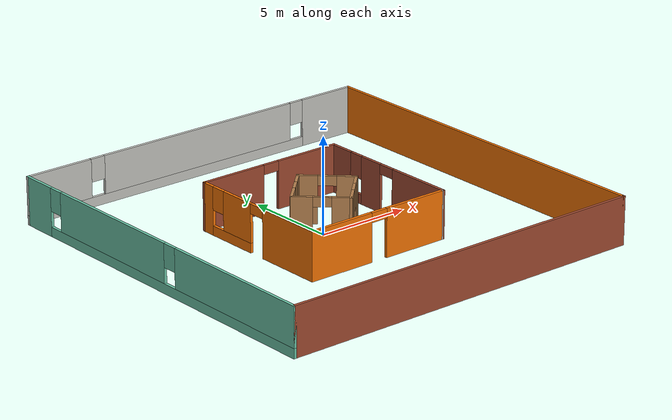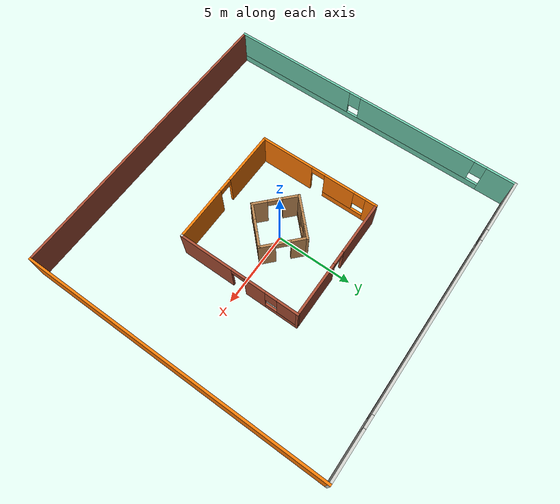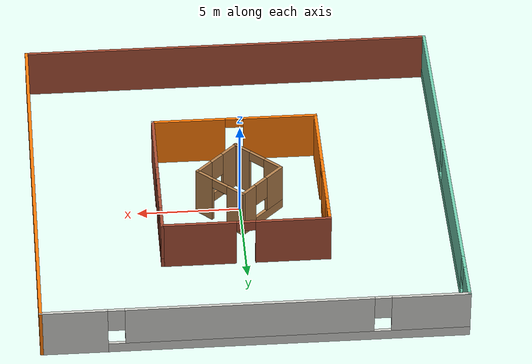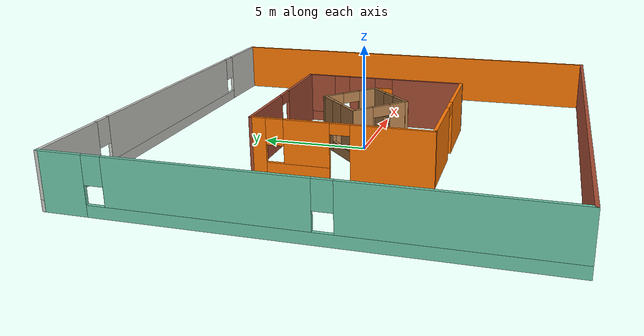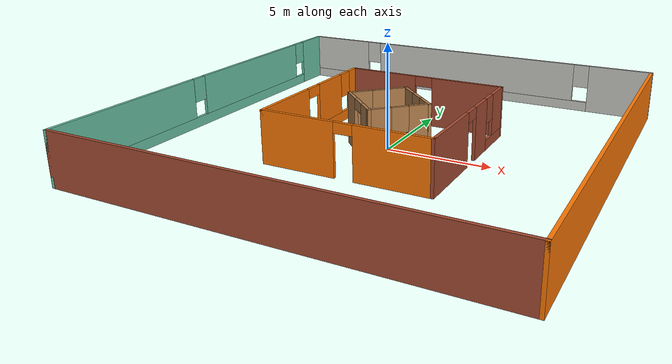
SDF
<?xml version='1.0'?>
<sdf version='1.6'>
  <model name='walls'>
    <link name='Wall_44'>
      <pose frame=''>0 -10 0 0 -0 0</pose>
      <self_collide>0</self_collide>
      <kinematic>0</kinematic>
      <visual name='Wall_44_Visual'>
        <pose frame=''>0 0 1.25 0 -0 0</pose>
        <geometry>
          <box>
            <size>20.15 0.15 2.5</size>
          </box>
        </geometry>
        <material>
          <script>
            <uri>file://media/materials/scripts/gazebo.material</uri>
            <name>Gazebo/Bricks</name>
          </script>
          <ambient>0.760784 0.662745 0.627451 1</ambient>
          <shader type='pixel'/>
          <diffuse>1 1 1 1</diffuse>
          <specular>0.2 0.2 0.2 1</specular>
          <emissive>0 0 0 1</emissive>
        </material>
        <meta>
          <layer>0</layer>
        </meta>
        <transparency>0</transparency>
        <cast_shadows>1</cast_shadows>
      </visual>
      <collision name='Wall_44_Collision'>
        <laser_retro>0</laser_retro>
        <max_contacts>10</max_contacts>
        <pose frame=''>0 0 1.25 0 -0 0</pose>
        <geometry>
          <box>
            <size>20.15 0.15 2.5</size>
          </box>
        </geometry>
        <surface>
          <friction>
            <ode>
              <mu>1</mu>
              <mu2>1</mu2>
              <fdir1>0 0 0</fdir1>
              <slip1>0</slip1>
              <slip2>0</slip2>
            </ode>
            <torsional>
              <coefficient>1</coefficient>
              <patch_radius>0</patch_radius>
              <surface_radius>0</surface_radius>
              <use_patch_radius>1</use_patch_radius>
              <ode>
                <slip>0</slip>
              </ode>
            </torsional>
          </friction>
          <bounce>
            <restitution_coefficient>0</restitution_coefficient>
            <threshold>1e+06</threshold>
          </bounce>
          <contact>
            <collide_without_contact>0</collide_without_contact>
            <collide_without_contact_bitmask>1</collide_without_contact_bitmask>
            <collide_bitmask>1</collide_bitmask>
            <ode>
              <soft_cfm>0</soft_cfm>
              <soft_erp>0.2</soft_erp>
              <kp>1e+13</kp>
              <kd>1</kd>
              <max_vel>0.01</max_vel>
              <min_depth>0</min_depth>
            </ode>
            <bullet>
              <split_impulse>1</split_impulse>
              <split_impulse_penetration_threshold>-0.01</split_impulse_penetration_threshold>
              <soft_cfm>0</soft_cfm>
              <soft_erp>0.2</soft_erp>
              <kp>1e+13</kp>
              <kd>1</kd>
            </bullet>
          </contact>
        </surface>
      </collision>
    </link>
    <link name='Wall_45'>
      <pose frame=''>10 0 0 0 -0 1.5708</pose>
      <self_collide>0</self_collide>
      <kinematic>0</kinematic>
      <visual name='Wall_45_Visual'>
        <pose frame=''>0 0 1.25 0 -0 0</pose>
        <geometry>
          <box>
            <size>20.15 0.15 2.5</size>
          </box>
        </geometry>
        <material>
          <script>
            <uri>file://media/materials/scripts/gazebo.material</uri>
            <name>Gazebo/Grey</name>
          </script>
          <ambient>0.996078 0.47451 0.0196078 1</ambient>
          <shader type='pixel'/>
          <diffuse>0.7 0.7 0.7 1</diffuse>
          <specular>0.01 0.01 0.01 1</specular>
          <emissive>0 0 0 1</emissive>
        </material>
        <meta>
          <layer>0</layer>
        </meta>
        <transparency>0</transparency>
        <cast_shadows>1</cast_shadows>
      </visual>
      <collision name='Wall_45_Collision'>
        <laser_retro>0</laser_retro>
        <max_contacts>10</max_contacts>
        <pose frame=''>0 0 1.25 0 -0 0</pose>
        <geometry>
          <box>
            <size>20.15 0.15 2.5</size>
          </box>
        </geometry>
        <surface>
          <friction>
            <ode>
              <mu>1</mu>
              <mu2>1</mu2>
              <fdir1>0 0 0</fdir1>
              <slip1>0</slip1>
              <slip2>0</slip2>
            </ode>
            <torsional>
              <coefficient>1</coefficient>
              <patch_radius>0</patch_radius>
              <surface_radius>0</surface_radius>
              <use_patch_radius>1</use_patch_radius>
              <ode>
                <slip>0</slip>
              </ode>
            </torsional>
          </friction>
          <bounce>
            <restitution_coefficient>0</restitution_coefficient>
            <threshold>1e+06</threshold>
          </bounce>
          <contact>
            <collide_without_contact>0</collide_without_contact>
            <collide_without_contact_bitmask>1</collide_without_contact_bitmask>
            <collide_bitmask>1</collide_bitmask>
            <ode>
              <soft_cfm>0</soft_cfm>
              <soft_erp>0.2</soft_erp>
              <kp>1e+13</kp>
              <kd>1</kd>
              <max_vel>0.01</max_vel>
              <min_depth>0</min_depth>
            </ode>
            <bullet>
              <split_impulse>1</split_impulse>
              <split_impulse_penetration_threshold>-0.01</split_impulse_penetration_threshold>
              <soft_cfm>0</soft_cfm>
              <soft_erp>0.2</soft_erp>
              <kp>1e+13</kp>
              <kd>1</kd>
            </bullet>
          </contact>
        </surface>
      </collision>
    </link>
    <link name='Wall_46'>
      <pose frame=''>0 10 0 0 -0 3.14159</pose>
      <self_collide>0</self_collide>
      <kinematic>0</kinematic>
      <visual name='Wall_46_Visual_0'>
        <pose frame=''>-8.48027 0 1.25 0 -0 0</pose>
        <geometry>
          <box>
            <size>3.18945 0.15 2.5</size>
          </box>
        </geometry>
        <material>
          <script>
            <uri>file://media/materials/scripts/gazebo.material</uri>
            <name>Gazebo/CeilingTiled</name>
          </script>
          <ambient>0.333333 0 1 1</ambient>
          <shader type='pixel'/>
          <diffuse>1 1 1 1</diffuse>
          <specular>0 0 0 1</specular>
          <emissive>0 0 0 1</emissive>
        </material>
        <meta>
          <layer>0</layer>
        </meta>
        <transparency>0</transparency>
        <cast_shadows>1</cast_shadows>
      </visual>
      <visual name='Wall_46_Visual_1'>
        <pose frame=''>1.59473 0 0.25 0 -0 0</pose>
        <geometry>
          <box>
            <size>16.9605 0.15 0.5</size>
          </box>
        </geometry>
        <material>
          <script>
            <uri>file://media/materials/scripts/gazebo.material</uri>
            <name>Gazebo/CeilingTiled</name>
          </script>
          <ambient>0.333333 0 1 1</ambient>
          <shader type='pixel'/>
          <diffuse>1 1 1 1</diffuse>
          <specular>0 0 0 1</specular>
          <emissive>0 0 0 1</emissive>
        </material>
        <meta>
          <layer>0</layer>
        </meta>
        <transparency>0</transparency>
        <cast_shadows>1</cast_shadows>
      </visual>
      <visual name='Wall_46_Visual_2'>
        <pose frame=''>-0.261101 0 1.5 0 -0 0</pose>
        <geometry>
          <box>
            <size>11.6489 0.15 2</size>
          </box>
        </geometry>
        <material>
          <script>
            <uri>file://media/materials/scripts/gazebo.material</uri>
            <name>Gazebo/CeilingTiled</name>
          </script>
          <ambient>0.333333 0 1 1</ambient>
          <shader type='pixel'/>
          <diffuse>1 1 1 1</diffuse>
          <specular>0 0 0 1</specular>
          <emissive>0 0 0 1</emissive>
        </material>
        <meta>
          <layer>0</layer>
        </meta>
        <transparency>0</transparency>
        <cast_shadows>1</cast_shadows>
      </visual>
      <visual name='Wall_46_Visual_3'>
        <pose frame=''>8.21917 0 1.5 0 -0 0</pose>
        <geometry>
          <box>
            <size>3.71165 0.15 2</size>
          </box>
        </geometry>
        <material>
          <script>
            <uri>file://media/materials/scripts/gazebo.material</uri>
            <name>Gazebo/CeilingTiled</name>
          </script>
          <ambient>0.333333 0 1 1</ambient>
          <shader type='pixel'/>
          <diffuse>1 1 1 1</diffuse>
          <specular>0 0 0 1</specular>
          <emissive>0 0 0 1</emissive>
        </material>
        <meta>
          <layer>0</layer>
        </meta>
        <transparency>0</transparency>
        <cast_shadows>1</cast_shadows>
      </visual>
      <visual name='Wall_46_Visual_4'>
        <pose frame=''>-6.48555 0 1.9 0 -0 0</pose>
        <geometry>
          <box>
            <size>0.8 0.15 1.2</size>
          </box>
        </geometry>
        <material>
          <script>
            <uri>file://media/materials/scripts/gazebo.material</uri>
            <name>Gazebo/CeilingTiled</name>
          </script>
          <ambient>0.333333 0 1 1</ambient>
          <shader type='pixel'/>
          <diffuse>1 1 1 1</diffuse>
          <specular>0 0 0 1</specular>
          <emissive>0 0 0 1</emissive>
        </material>
        <meta>
          <layer>0</layer>
        </meta>
        <transparency>0</transparency>
        <cast_shadows>1</cast_shadows>
      </visual>
      <visual name='Wall_46_Visual_5'>
        <pose frame=''>5.96335 0 1.9 0 -0 0</pose>
        <geometry>
          <box>
            <size>0.8 0.15 1.2</size>
          </box>
        </geometry>
        <material>
          <script>
            <uri>file://media/materials/scripts/gazebo.material</uri>
            <name>Gazebo/CeilingTiled</name>
          </script>
          <ambient>0.333333 0 1 1</ambient>
          <shader type='pixel'/>
          <diffuse>1 1 1 1</diffuse>
          <specular>0 0 0 1</specular>
          <emissive>0 0 0 1</emissive>
        </material>
        <meta>
          <layer>0</layer>
        </meta>
        <transparency>0</transparency>
        <cast_shadows>1</cast_shadows>
      </visual>
      <collision name='Wall_46_Collision_0'>
        <laser_retro>0</laser_retro>
        <max_contacts>10</max_contacts>
        <pose frame=''>-8.48027 0 1.25 0 -0 0</pose>
        <geometry>
          <box>
            <size>3.18945 0.15 2.5</size>
          </box>
        </geometry>
        <surface>
          <friction>
            <ode>
              <mu>1</mu>
              <mu2>1</mu2>
              <fdir1>0 0 0</fdir1>
              <slip1>0</slip1>
              <slip2>0</slip2>
            </ode>
            <torsional>
              <coefficient>1</coefficient>
              <patch_radius>0</patch_radius>
              <surface_radius>0</surface_radius>
              <use_patch_radius>1</use_patch_radius>
              <ode>
                <slip>0</slip>
              </ode>
            </torsional>
          </friction>
          <bounce>
            <restitution_coefficient>0</restitution_coefficient>
            <threshold>1e+06</threshold>
          </bounce>
          <contact>
            <collide_without_contact>0</collide_without_contact>
            <collide_without_contact_bitmask>1</collide_without_contact_bitmask>
            <collide_bitmask>1</collide_bitmask>
            <ode>
              <soft_cfm>0</soft_cfm>
              <soft_erp>0.2</soft_erp>
              <kp>1e+13</kp>
              <kd>1</kd>
              <max_vel>0.01</max_vel>
              <min_depth>0</min_depth>
            </ode>
            <bullet>
              <split_impulse>1</split_impulse>
              <split_impulse_penetration_threshold>-0.01</split_impulse_penetration_threshold>
              <soft_cfm>0</soft_cfm>
              <soft_erp>0.2</soft_erp>
              <kp>1e+13</kp>
              <kd>1</kd>
            </bullet>
          </contact>
        </surface>
      </collision>
      <collision name='Wall_46_Collision_1'>
        <laser_retro>0</laser_retro>
        <max_contacts>10</max_contacts>
        <pose frame=''>1.59473 0 0.25 0 -0 0</pose>
        <geometry>
          <box>
            <size>16.9605 0.15 0.5</size>
          </box>
        </geometry>
        <surface>
          <friction>
            <ode>
              <mu>1</mu>
              <mu2>1</mu2>
              <fdir1>0 0 0</fdir1>
              <slip1>0</slip1>
              <slip2>0</slip2>
            </ode>
            <torsional>
              <coefficient>1</coefficient>
              <patch_radius>0</patch_radius>
              <surface_radius>0</surface_radius>
              <use_patch_radius>1</use_patch_radius>
              <ode>
                <slip>0</slip>
              </ode>
            </torsional>
          </friction>
          <bounce>
            <restitution_coefficient>0</restitution_coefficient>
            <threshold>1e+06</threshold>
          </bounce>
          <contact>
            <collide_without_contact>0</collide_without_contact>
            <collide_without_contact_bitmask>1</collide_without_contact_bitmask>
            <collide_bitmask>1</collide_bitmask>
            <ode>
              <soft_cfm>0</soft_cfm>
              <soft_erp>0.2</soft_erp>
              <kp>1e+13</kp>
              <kd>1</kd>
              <max_vel>0.01</max_vel>
              <min_depth>0</min_depth>
            </ode>
            <bullet>
              <split_impulse>1</split_impulse>
              <split_impulse_penetration_threshold>-0.01</split_impulse_penetration_threshold>
              <soft_cfm>0</soft_cfm>
              <soft_erp>0.2</soft_erp>
              <kp>1e+13</kp>
              <kd>1</kd>
            </bullet>
          </contact>
        </surface>
      </collision>
      <collision name='Wall_46_Collision_2'>
        <laser_retro>0</laser_retro>
        <max_contacts>10</max_contacts>
        <pose frame=''>-0.261101 0 1.5 0 -0 0</pose>
        <geometry>
          <box>
            <size>11.6489 0.15 2</size>
          </box>
        </geometry>
        <surface>
          <friction>
            <ode>
              <mu>1</mu>
              <mu2>1</mu2>
              <fdir1>0 0 0</fdir1>
              <slip1>0</slip1>
              <slip2>0</slip2>
            </ode>
            <torsional>
              <coefficient>1</coefficient>
              <patch_radius>0</patch_radius>
              <surface_radius>0</surface_radius>
              <use_patch_radius>1</use_patch_radius>
              <ode>
                <slip>0</slip>
              </ode>
            </torsional>
          </friction>
          <bounce>
            <restitution_coefficient>0</restitution_coefficient>
            <threshold>1e+06</threshold>
          </bounce>
          <contact>
            <collide_without_contact>0</collide_without_contact>
            <collide_without_contact_bitmask>1</collide_without_contact_bitmask>
            <collide_bitmask>1</collide_bitmask>
            <ode>
              <soft_cfm>0</soft_cfm>
              <soft_erp>0.2</soft_erp>
              <kp>1e+13</kp>
              <kd>1</kd>
              <max_vel>0.01</max_vel>
              <min_depth>0</min_depth>
            </ode>
            <bullet>
              <split_impulse>1</split_impulse>
              <split_impulse_penetration_threshold>-0.01</split_impulse_penetration_threshold>
              <soft_cfm>0</soft_cfm>
              <soft_erp>0.2</soft_erp>
              <kp>1e+13</kp>
              <kd>1</kd>
            </bullet>
          </contact>
        </surface>
      </collision>
      <collision name='Wall_46_Collision_3'>
        <laser_retro>0</laser_retro>
        <max_contacts>10</max_contacts>
        <pose frame=''>8.21917 0 1.5 0 -0 0</pose>
        <geometry>
          <box>
            <size>3.71165 0.15 2</size>
          </box>
        </geometry>
        <surface>
          <friction>
            <ode>
              <mu>1</mu>
              <mu2>1</mu2>
              <fdir1>0 0 0</fdir1>
              <slip1>0</slip1>
              <slip2>0</slip2>
            </ode>
            <torsional>
              <coefficient>1</coefficient>
              <patch_radius>0</patch_radius>
              <surface_radius>0</surface_radius>
              <use_patch_radius>1</use_patch_radius>
              <ode>
                <slip>0</slip>
              </ode>
            </torsional>
          </friction>
          <bounce>
            <restitution_coefficient>0</restitution_coefficient>
            <threshold>1e+06</threshold>
          </bounce>
          <contact>
            <collide_without_contact>0</collide_without_contact>
            <collide_without_contact_bitmask>1</collide_without_contact_bitmask>
            <collide_bitmask>1</collide_bitmask>
            <ode>
              <soft_cfm>0</soft_cfm>
              <soft_erp>0.2</soft_erp>
              <kp>1e+13</kp>
              <kd>1</kd>
              <max_vel>0.01</max_vel>
              <min_depth>0</min_depth>
            </ode>
            <bullet>
              <split_impulse>1</split_impulse>
              <split_impulse_penetration_threshold>-0.01</split_impulse_penetration_threshold>
              <soft_cfm>0</soft_cfm>
              <soft_erp>0.2</soft_erp>
              <kp>1e+13</kp>
              <kd>1</kd>
            </bullet>
          </contact>
        </surface>
      </collision>
      <collision name='Wall_46_Collision_4'>
        <laser_retro>0</laser_retro>
        <max_contacts>10</max_contacts>
        <pose frame=''>-6.48555 0 1.9 0 -0 0</pose>
        <geometry>
          <box>
            <size>0.8 0.15 1.2</size>
          </box>
        </geometry>
        <surface>
          <friction>
            <ode>
              <mu>1</mu>
              <mu2>1</mu2>
              <fdir1>0 0 0</fdir1>
              <slip1>0</slip1>
              <slip2>0</slip2>
            </ode>
            <torsional>
              <coefficient>1</coefficient>
              <patch_radius>0</patch_radius>
              <surface_radius>0</surface_radius>
              <use_patch_radius>1</use_patch_radius>
              <ode>
                <slip>0</slip>
              </ode>
            </torsional>
          </friction>
          <bounce>
            <restitution_coefficient>0</restitution_coefficient>
            <threshold>1e+06</threshold>
          </bounce>
          <contact>
            <collide_without_contact>0</collide_without_contact>
            <collide_without_contact_bitmask>1</collide_without_contact_bitmask>
            <collide_bitmask>1</collide_bitmask>
            <ode>
              <soft_cfm>0</soft_cfm>
              <soft_erp>0.2</soft_erp>
              <kp>1e+13</kp>
              <kd>1</kd>
              <max_vel>0.01</max_vel>
              <min_depth>0</min_depth>
            </ode>
            <bullet>
              <split_impulse>1</split_impulse>
              <split_impulse_penetration_threshold>-0.01</split_impulse_penetration_threshold>
              <soft_cfm>0</soft_cfm>
              <soft_erp>0.2</soft_erp>
              <kp>1e+13</kp>
              <kd>1</kd>
            </bullet>
          </contact>
        </surface>
      </collision>
      <collision name='Wall_46_Collision_5'>
        <laser_retro>0</laser_retro>
        <max_contacts>10</max_contacts>
        <pose frame=''>5.96335 0 1.9 0 -0 0</pose>
        <geometry>
          <box>
            <size>0.8 0.15 1.2</size>
          </box>
        </geometry>
        <surface>
          <friction>
            <ode>
              <mu>1</mu>
              <mu2>1</mu2>
              <fdir1>0 0 0</fdir1>
              <slip1>0</slip1>
              <slip2>0</slip2>
            </ode>
            <torsional>
              <coefficient>1</coefficient>
              <patch_radius>0</patch_radius>
              <surface_radius>0</surface_radius>
              <use_patch_radius>1</use_patch_radius>
              <ode>
                <slip>0</slip>
              </ode>
            </torsional>
          </friction>
          <bounce>
            <restitution_coefficient>0</restitution_coefficient>
            <threshold>1e+06</threshold>
          </bounce>
          <contact>
            <collide_without_contact>0</collide_without_contact>
            <collide_without_contact_bitmask>1</collide_without_contact_bitmask>
            <collide_bitmask>1</collide_bitmask>
            <ode>
              <soft_cfm>0</soft_cfm>
              <soft_erp>0.2</soft_erp>
              <kp>1e+13</kp>
              <kd>1</kd>
              <max_vel>0.01</max_vel>
              <min_depth>0</min_depth>
            </ode>
            <bullet>
              <split_impulse>1</split_impulse>
              <split_impulse_penetration_threshold>-0.01</split_impulse_penetration_threshold>
              <soft_cfm>0</soft_cfm>
              <soft_erp>0.2</soft_erp>
              <kp>1e+13</kp>
              <kd>1</kd>
            </bullet>
          </contact>
        </surface>
      </collision>
    </link>
    <link name='Wall_47'>
      <pose frame=''>-10 0 0 0 0 -1.5708</pose>
      <self_collide>0</self_collide>
      <kinematic>0</kinematic>
      <visual name='Wall_47_Visual_0'>
        <pose frame=''>-9.08483 0 1.25 0 -0 0</pose>
        <geometry>
          <box>
            <size>1.98033 0.15 2.5</size>
          </box>
        </geometry>
        <material>
          <script>
            <uri>file://media/materials/scripts/gazebo.material</uri>
            <name>Gazebo/Grey</name>
          </script>
          <ambient>0.435294 0.796078 0.67451 1</ambient>
          <shader type='pixel'/>
          <diffuse>0.7 0.7 0.7 1</diffuse>
          <specular>0.01 0.01 0.01 1</specular>
          <emissive>0 0 0 1</emissive>
        </material>
        <meta>
          <layer>0</layer>
        </meta>
        <transparency>0</transparency>
        <cast_shadows>1</cast_shadows>
      </visual>
      <visual name='Wall_47_Visual_1'>
        <pose frame=''>0.990168 0 0.25 0 -0 0</pose>
        <geometry>
          <box>
            <size>18.1697 0.15 0.5</size>
          </box>
        </geometry>
        <material>
          <script>
            <uri>file://media/materials/scripts/gazebo.material</uri>
            <name>Gazebo/Grey</name>
          </script>
          <ambient>0.435294 0.796078 0.67451 1</ambient>
          <shader type='pixel'/>
          <diffuse>0.7 0.7 0.7 1</diffuse>
          <specular>0.01 0.01 0.01 1</specular>
          <emissive>0 0 0 1</emissive>
        </material>
        <meta>
          <layer>0</layer>
        </meta>
        <transparency>0</transparency>
        <cast_shadows>1</cast_shadows>
      </visual>
      <visual name='Wall_47_Visual_2'>
        <pose frame=''>-3.25243 0 1.5 0 -0 0</pose>
        <geometry>
          <box>
            <size>8.08447 0.15 2</size>
          </box>
        </geometry>
        <material>
          <script>
            <uri>file://media/materials/scripts/gazebo.material</uri>
            <name>Gazebo/Grey</name>
          </script>
          <ambient>0.435294 0.796078 0.67451 1</ambient>
          <shader type='pixel'/>
          <diffuse>0.7 0.7 0.7 1</diffuse>
          <specular>0.01 0.01 0.01 1</specular>
          <emissive>0 0 0 1</emissive>
        </material>
        <meta>
          <layer>0</layer>
        </meta>
        <transparency>0</transparency>
        <cast_shadows>1</cast_shadows>
      </visual>
      <visual name='Wall_47_Visual_3'>
        <pose frame=''>5.8324 0 1.5 0 -0 0</pose>
        <geometry>
          <box>
            <size>8.4852 0.15 2</size>
          </box>
        </geometry>
        <material>
          <script>
            <uri>file://media/materials/scripts/gazebo.material</uri>
            <name>Gazebo/Grey</name>
          </script>
          <ambient>0.435294 0.796078 0.67451 1</ambient>
          <shader type='pixel'/>
          <diffuse>0.7 0.7 0.7 1</diffuse>
          <specular>0.01 0.01 0.01 1</specular>
          <emissive>0 0 0 1</emissive>
        </material>
        <meta>
          <layer>0</layer>
        </meta>
        <transparency>0</transparency>
        <cast_shadows>1</cast_shadows>
      </visual>
      <visual name='Wall_47_Visual_4'>
        <pose frame=''>-7.69466 0 1.9 0 -0 0</pose>
        <geometry>
          <box>
            <size>0.8 0.15 1.2</size>
          </box>
        </geometry>
        <material>
          <script>
            <uri>file://media/materials/scripts/gazebo.material</uri>
            <name>Gazebo/Grey</name>
          </script>
          <ambient>0.435294 0.796078 0.67451 1</ambient>
          <shader type='pixel'/>
          <diffuse>0.7 0.7 0.7 1</diffuse>
          <specular>0.01 0.01 0.01 1</specular>
          <emissive>0 0 0 1</emissive>
        </material>
        <meta>
          <layer>0</layer>
        </meta>
        <transparency>0</transparency>
        <cast_shadows>1</cast_shadows>
      </visual>
      <visual name='Wall_47_Visual_5'>
        <pose frame=''>1.1898 0 1.9 0 -0 0</pose>
        <geometry>
          <box>
            <size>0.8 0.15 1.2</size>
          </box>
        </geometry>
        <material>
          <script>
            <uri>file://media/materials/scripts/gazebo.material</uri>
            <name>Gazebo/Grey</name>
          </script>
          <ambient>0.435294 0.796078 0.67451 1</ambient>
          <shader type='pixel'/>
          <diffuse>0.7 0.7 0.7 1</diffuse>
          <specular>0.01 0.01 0.01 1</specular>
          <emissive>0 0 0 1</emissive>
        </material>
        <meta>
          <layer>0</layer>
        </meta>
        <transparency>0</transparency>
        <cast_shadows>1</cast_shadows>
      </visual>
      <collision name='Wall_47_Collision_0'>
        <laser_retro>0</laser_retro>
        <max_contacts>10</max_contacts>
        <pose frame=''>-9.08483 0 1.25 0 -0 0</pose>
        <geometry>
          <box>
            <size>1.98033 0.15 2.5</size>
          </box>
        </geometry>
        <surface>
          <friction>
            <ode>
              <mu>1</mu>
              <mu2>1</mu2>
              <fdir1>0 0 0</fdir1>
              <slip1>0</slip1>
              <slip2>0</slip2>
            </ode>
            <torsional>
              <coefficient>1</coefficient>
              <patch_radius>0</patch_radius>
              <surface_radius>0</surface_radius>
              <use_patch_radius>1</use_patch_radius>
              <ode>
                <slip>0</slip>
              </ode>
            </torsional>
          </friction>
          <bounce>
            <restitution_coefficient>0</restitution_coefficient>
            <threshold>1e+06</threshold>
          </bounce>
          <contact>
            <collide_without_contact>0</collide_without_contact>
            <collide_without_contact_bitmask>1</collide_without_contact_bitmask>
            <collide_bitmask>1</collide_bitmask>
            <ode>
              <soft_cfm>0</soft_cfm>
              <soft_erp>0.2</soft_erp>
              <kp>1e+13</kp>
              <kd>1</kd>
              <max_vel>0.01</max_vel>
              <min_depth>0</min_depth>
            </ode>
            <bullet>
              <split_impulse>1</split_impulse>
              <split_impulse_penetration_threshold>-0.01</split_impulse_penetration_threshold>
              <soft_cfm>0</soft_cfm>
              <soft_erp>0.2</soft_erp>
              <kp>1e+13</kp>
              <kd>1</kd>
            </bullet>
          </contact>
        </surface>
      </collision>
      <collision name='Wall_47_Collision_1'>
        <laser_retro>0</laser_retro>
        <max_contacts>10</max_contacts>
        <pose frame=''>0.990168 0 0.25 0 -0 0</pose>
        <geometry>
          <box>
            <size>18.1697 0.15 0.5</size>
          </box>
        </geometry>
        <surface>
          <friction>
            <ode>
              <mu>1</mu>
              <mu2>1</mu2>
              <fdir1>0 0 0</fdir1>
              <slip1>0</slip1>
              <slip2>0</slip2>
            </ode>
            <torsional>
              <coefficient>1</coefficient>
              <patch_radius>0</patch_radius>
              <surface_radius>0</surface_radius>
              <use_patch_radius>1</use_patch_radius>
              <ode>
                <slip>0</slip>
              </ode>
            </torsional>
          </friction>
          <bounce>
            <restitution_coefficient>0</restitution_coefficient>
            <threshold>1e+06</threshold>
          </bounce>
          <contact>
            <collide_without_contact>0</collide_without_contact>
            <collide_without_contact_bitmask>1</collide_without_contact_bitmask>
            <collide_bitmask>1</collide_bitmask>
            <ode>
              <soft_cfm>0</soft_cfm>
              <soft_erp>0.2</soft_erp>
              <kp>1e+13</kp>
              <kd>1</kd>
              <max_vel>0.01</max_vel>
              <min_depth>0</min_depth>
            </ode>
            <bullet>
              <split_impulse>1</split_impulse>
              <split_impulse_penetration_threshold>-0.01</split_impulse_penetration_threshold>
              <soft_cfm>0</soft_cfm>
              <soft_erp>0.2</soft_erp>
              <kp>1e+13</kp>
              <kd>1</kd>
            </bullet>
          </contact>
        </surface>
      </collision>
      <collision name='Wall_47_Collision_2'>
        <laser_retro>0</laser_retro>
        <max_contacts>10</max_contacts>
        <pose frame=''>-3.25243 0 1.5 0 -0 0</pose>
        <geometry>
          <box>
            <size>8.08447 0.15 2</size>
          </box>
        </geometry>
        <surface>
          <friction>
            <ode>
              <mu>1</mu>
              <mu2>1</mu2>
              <fdir1>0 0 0</fdir1>
              <slip1>0</slip1>
              <slip2>0</slip2>
            </ode>
            <torsional>
              <coefficient>1</coefficient>
              <patch_radius>0</patch_radius>
              <surface_radius>0</surface_radius>
              <use_patch_radius>1</use_patch_radius>
              <ode>
                <slip>0</slip>
              </ode>
            </torsional>
          </friction>
          <bounce>
            <restitution_coefficient>0</restitution_coefficient>
            <threshold>1e+06</threshold>
          </bounce>
          <contact>
            <collide_without_contact>0</collide_without_contact>
            <collide_without_contact_bitmask>1</collide_without_contact_bitmask>
            <collide_bitmask>1</collide_bitmask>
            <ode>
              <soft_cfm>0</soft_cfm>
              <soft_erp>0.2</soft_erp>
              <kp>1e+13</kp>
              <kd>1</kd>
              <max_vel>0.01</max_vel>
              <min_depth>0</min_depth>
            </ode>
            <bullet>
              <split_impulse>1</split_impulse>
              <split_impulse_penetration_threshold>-0.01</split_impulse_penetration_threshold>
              <soft_cfm>0</soft_cfm>
              <soft_erp>0.2</soft_erp>
              <kp>1e+13</kp>
              <kd>1</kd>
            </bullet>
          </contact>
        </surface>
      </collision>
      <collision name='Wall_47_Collision_3'>
        <laser_retro>0</laser_retro>
        <max_contacts>10</max_contacts>
        <pose frame=''>5.8324 0 1.5 0 -0 0</pose>
        <geometry>
          <box>
            <size>8.4852 0.15 2</size>
          </box>
        </geometry>
        <surface>
          <friction>
            <ode>
              <mu>1</mu>
              <mu2>1</mu2>
              <fdir1>0 0 0</fdir1>
              <slip1>0</slip1>
              <slip2>0</slip2>
            </ode>
            <torsional>
              <coefficient>1</coefficient>
              <patch_radius>0</patch_radius>
              <surface_radius>0</surface_radius>
              <use_patch_radius>1</use_patch_radius>
              <ode>
                <slip>0</slip>
              </ode>
            </torsional>
          </friction>
          <bounce>
            <restitution_coefficient>0</restitution_coefficient>
            <threshold>1e+06</threshold>
          </bounce>
          <contact>
            <collide_without_contact>0</collide_without_contact>
            <collide_without_contact_bitmask>1</collide_without_contact_bitmask>
            <collide_bitmask>1</collide_bitmask>
            <ode>
              <soft_cfm>0</soft_cfm>
              <soft_erp>0.2</soft_erp>
              <kp>1e+13</kp>
              <kd>1</kd>
              <max_vel>0.01</max_vel>
              <min_depth>0</min_depth>
            </ode>
            <bullet>
              <split_impulse>1</split_impulse>
              <split_impulse_penetration_threshold>-0.01</split_impulse_penetration_threshold>
              <soft_cfm>0</soft_cfm>
              <soft_erp>0.2</soft_erp>
              <kp>1e+13</kp>
              <kd>1</kd>
            </bullet>
          </contact>
        </surface>
      </collision>
      <collision name='Wall_47_Collision_4'>
        <laser_retro>0</laser_retro>
        <max_contacts>10</max_contacts>
        <pose frame=''>-7.69466 0 1.9 0 -0 0</pose>
        <geometry>
          <box>
            <size>0.8 0.15 1.2</size>
          </box>
        </geometry>
        <surface>
          <friction>
            <ode>
              <mu>1</mu>
              <mu2>1</mu2>
              <fdir1>0 0 0</fdir1>
              <slip1>0</slip1>
              <slip2>0</slip2>
            </ode>
            <torsional>
              <coefficient>1</coefficient>
              <patch_radius>0</patch_radius>
              <surface_radius>0</surface_radius>
              <use_patch_radius>1</use_patch_radius>
              <ode>
                <slip>0</slip>
              </ode>
            </torsional>
          </friction>
          <bounce>
            <restitution_coefficient>0</restitution_coefficient>
            <threshold>1e+06</threshold>
          </bounce>
          <contact>
            <collide_without_contact>0</collide_without_contact>
            <collide_without_contact_bitmask>1</collide_without_contact_bitmask>
            <collide_bitmask>1</collide_bitmask>
            <ode>
              <soft_cfm>0</soft_cfm>
              <soft_erp>0.2</soft_erp>
              <kp>1e+13</kp>
              <kd>1</kd>
              <max_vel>0.01</max_vel>
              <min_depth>0</min_depth>
            </ode>
            <bullet>
              <split_impulse>1</split_impulse>
              <split_impulse_penetration_threshold>-0.01</split_impulse_penetration_threshold>
              <soft_cfm>0</soft_cfm>
              <soft_erp>0.2</soft_erp>
              <kp>1e+13</kp>
              <kd>1</kd>
            </bullet>
          </contact>
        </surface>
      </collision>
      <collision name='Wall_47_Collision_5'>
        <laser_retro>0</laser_retro>
        <max_contacts>10</max_contacts>
        <pose frame=''>1.1898 0 1.9 0 -0 0</pose>
        <geometry>
          <box>
            <size>0.8 0.15 1.2</size>
          </box>
        </geometry>
        <surface>
          <friction>
            <ode>
              <mu>1</mu>
              <mu2>1</mu2>
              <fdir1>0 0 0</fdir1>
              <slip1>0</slip1>
              <slip2>0</slip2>
            </ode>
            <torsional>
              <coefficient>1</coefficient>
              <patch_radius>0</patch_radius>
              <surface_radius>0</surface_radius>
              <use_patch_radius>1</use_patch_radius>
              <ode>
                <slip>0</slip>
              </ode>
            </torsional>
          </friction>
          <bounce>
            <restitution_coefficient>0</restitution_coefficient>
            <threshold>1e+06</threshold>
          </bounce>
          <contact>
            <collide_without_contact>0</collide_without_contact>
            <collide_without_contact_bitmask>1</collide_without_contact_bitmask>
            <collide_bitmask>1</collide_bitmask>
            <ode>
              <soft_cfm>0</soft_cfm>
              <soft_erp>0.2</soft_erp>
              <kp>1e+13</kp>
              <kd>1</kd>
              <max_vel>0.01</max_vel>
              <min_depth>0</min_depth>
            </ode>
            <bullet>
              <split_impulse>1</split_impulse>
              <split_impulse_penetration_threshold>-0.01</split_impulse_penetration_threshold>
              <soft_cfm>0</soft_cfm>
              <soft_erp>0.2</soft_erp>
              <kp>1e+13</kp>
              <kd>1</kd>
            </bullet>
          </contact>
        </surface>
      </collision>
    </link>
    <link name='Wall_49'>
      <pose frame=''>-4 0 0 0 0 -1.5708</pose>
      <self_collide>0</self_collide>
      <kinematic>0</kinematic>
      <visual name='Wall_49_Visual_0'>
        <pose frame=''>-3.69081 0 1.25 0 -0 0</pose>
        <geometry>
          <box>
            <size>0.768371 0.15 2.5</size>
          </box>
        </geometry>
        <material>
          <script>
            <uri>file://media/materials/scripts/gazebo.material</uri>
            <name>Gazebo/Grey</name>
          </script>
          <ambient>0.996078 0.47451 0.0196078 1</ambient>
          <shader type='pixel'/>
          <diffuse>0.7 0.7 0.7 1</diffuse>
          <specular>0.01 0.01 0.01 1</specular>
          <emissive>0 0 0 1</emissive>
        </material>
        <meta>
          <layer>0</layer>
        </meta>
        <transparency>0</transparency>
        <cast_shadows>1</cast_shadows>
      </visual>
      <visual name='Wall_49_Visual_1'>
        <pose frame=''>2.2625 0 1.25 0 -0 0</pose>
        <geometry>
          <box>
            <size>3.625 0.15 2.5</size>
          </box>
        </geometry>
        <material>
          <script>
            <uri>file://media/materials/scripts/gazebo.material</uri>
            <name>Gazebo/Grey</name>
          </script>
          <ambient>0.996078 0.47451 0.0196078 1</ambient>
          <shader type='pixel'/>
          <diffuse>0.7 0.7 0.7 1</diffuse>
          <specular>0.01 0.01 0.01 1</specular>
          <emissive>0 0 0 1</emissive>
        </material>
        <meta>
          <layer>0</layer>
        </meta>
        <transparency>0</transparency>
        <cast_shadows>1</cast_shadows>
      </visual>
      <visual name='Wall_49_Visual_2'>
        <pose frame=''>-1.87831 0 0.25 0 -0 0</pose>
        <geometry>
          <box>
            <size>2.85663 0.15 0.5</size>
          </box>
        </geometry>
        <material>
          <script>
            <uri>file://media/materials/scripts/gazebo.material</uri>
            <name>Gazebo/Grey</name>
          </script>
          <ambient>0.996078 0.47451 0.0196078 1</ambient>
          <shader type='pixel'/>
          <diffuse>0.7 0.7 0.7 1</diffuse>
          <specular>0.01 0.01 0.01 1</specular>
          <emissive>0 0 0 1</emissive>
        </material>
        <meta>
          <layer>0</layer>
        </meta>
        <transparency>0</transparency>
        <cast_shadows>1</cast_shadows>
      </visual>
      <visual name='Wall_49_Visual_3'>
        <pose frame=''>-1.47831 0 1.5 0 -0 0</pose>
        <geometry>
          <box>
            <size>2.05663 0.15 2</size>
          </box>
        </geometry>
        <material>
          <script>
            <uri>file://media/materials/scripts/gazebo.material</uri>
            <name>Gazebo/Grey</name>
          </script>
          <ambient>0.996078 0.47451 0.0196078 1</ambient>
          <shader type='pixel'/>
          <diffuse>0.7 0.7 0.7 1</diffuse>
          <specular>0.01 0.01 0.01 1</specular>
          <emissive>0 0 0 1</emissive>
        </material>
        <meta>
          <layer>0</layer>
        </meta>
        <transparency>0</transparency>
        <cast_shadows>1</cast_shadows>
      </visual>
      <visual name='Wall_49_Visual_4'>
        <pose frame=''>-2.90663 0 1.9 0 -0 0</pose>
        <geometry>
          <box>
            <size>0.8 0.15 1.2</size>
          </box>
        </geometry>
        <material>
          <script>
            <uri>file://media/materials/scripts/gazebo.material</uri>
            <name>Gazebo/Grey</name>
          </script>
          <ambient>0.996078 0.47451 0.0196078 1</ambient>
          <shader type='pixel'/>
          <diffuse>0.7 0.7 0.7 1</diffuse>
          <specular>0.01 0.01 0.01 1</specular>
          <emissive>0 0 0 1</emissive>
        </material>
        <meta>
          <layer>0</layer>
        </meta>
        <transparency>0</transparency>
        <cast_shadows>1</cast_shadows>
      </visual>
      <visual name='Wall_49_Visual_5'>
        <pose frame=''>0 0 2.25 0 -0 0</pose>
        <geometry>
          <box>
            <size>0.9 0.15 0.5</size>
          </box>
        </geometry>
        <material>
          <script>
            <uri>file://media/materials/scripts/gazebo.material</uri>
            <name>Gazebo/Grey</name>
          </script>
          <ambient>0.996078 0.47451 0.0196078 1</ambient>
          <shader type='pixel'/>
          <diffuse>0.7 0.7 0.7 1</diffuse>
          <specular>0.01 0.01 0.01 1</specular>
          <emissive>0 0 0 1</emissive>
        </material>
        <meta>
          <layer>0</layer>
        </meta>
        <transparency>0</transparency>
        <cast_shadows>1</cast_shadows>
      </visual>
      <collision name='Wall_49_Collision_0'>
        <laser_retro>0</laser_retro>
        <max_contacts>10</max_contacts>
        <pose frame=''>-3.69081 0 1.25 0 -0 0</pose>
        <geometry>
          <box>
            <size>0.768371 0.15 2.5</size>
          </box>
        </geometry>
        <surface>
          <friction>
            <ode>
              <mu>1</mu>
              <mu2>1</mu2>
              <fdir1>0 0 0</fdir1>
              <slip1>0</slip1>
              <slip2>0</slip2>
            </ode>
            <torsional>
              <coefficient>1</coefficient>
              <patch_radius>0</patch_radius>
              <surface_radius>0</surface_radius>
              <use_patch_radius>1</use_patch_radius>
              <ode>
                <slip>0</slip>
              </ode>
            </torsional>
          </friction>
          <bounce>
            <restitution_coefficient>0</restitution_coefficient>
            <threshold>1e+06</threshold>
          </bounce>
          <contact>
            <collide_without_contact>0</collide_without_contact>
            <collide_without_contact_bitmask>1</collide_without_contact_bitmask>
            <collide_bitmask>1</collide_bitmask>
            <ode>
              <soft_cfm>0</soft_cfm>
              <soft_erp>0.2</soft_erp>
              <kp>1e+13</kp>
              <kd>1</kd>
              <max_vel>0.01</max_vel>
              <min_depth>0</min_depth>
            </ode>
            <bullet>
              <split_impulse>1</split_impulse>
              <split_impulse_penetration_threshold>-0.01</split_impulse_penetration_threshold>
              <soft_cfm>0</soft_cfm>
              <soft_erp>0.2</soft_erp>
              <kp>1e+13</kp>
              <kd>1</kd>
            </bullet>
          </contact>
        </surface>
      </collision>
      <collision name='Wall_49_Collision_1'>
        <laser_retro>0</laser_retro>
        <max_contacts>10</max_contacts>
        <pose frame=''>2.2625 0 1.25 0 -0 0</pose>
        <geometry>
          <box>
            <size>3.625 0.15 2.5</size>
          </box>
        </geometry>
        <surface>
          <friction>
            <ode>
              <mu>1</mu>
              <mu2>1</mu2>
              <fdir1>0 0 0</fdir1>
              <slip1>0</slip1>
              <slip2>0</slip2>
            </ode>
            <torsional>
              <coefficient>1</coefficient>
              <patch_radius>0</patch_radius>
              <surface_radius>0</surface_radius>
              <use_patch_radius>1</use_patch_radius>
              <ode>
                <slip>0</slip>
              </ode>
            </torsional>
          </friction>
          <bounce>
            <restitution_coefficient>0</restitution_coefficient>
            <threshold>1e+06</threshold>
          </bounce>
          <contact>
            <collide_without_contact>0</collide_without_contact>
            <collide_without_contact_bitmask>1</collide_without_contact_bitmask>
            <collide_bitmask>1</collide_bitmask>
            <ode>
              <soft_cfm>0</soft_cfm>
              <soft_erp>0.2</soft_erp>
              <kp>1e+13</kp>
              <kd>1</kd>
              <max_vel>0.01</max_vel>
              <min_depth>0</min_depth>
            </ode>
            <bullet>
              <split_impulse>1</split_impulse>
              <split_impulse_penetration_threshold>-0.01</split_impulse_penetration_threshold>
              <soft_cfm>0</soft_cfm>
              <soft_erp>0.2</soft_erp>
              <kp>1e+13</kp>
              <kd>1</kd>
            </bullet>
          </contact>
        </surface>
      </collision>
      <collision name='Wall_49_Collision_2'>
        <laser_retro>0</laser_retro>
        <max_contacts>10</max_contacts>
        <pose frame=''>-1.87831 0 0.25 0 -0 0</pose>
        <geometry>
          <box>
            <size>2.85663 0.15 0.5</size>
          </box>
        </geometry>
        <surface>
          <friction>
            <ode>
              <mu>1</mu>
              <mu2>1</mu2>
              <fdir1>0 0 0</fdir1>
              <slip1>0</slip1>
              <slip2>0</slip2>
            </ode>
            <torsional>
              <coefficient>1</coefficient>
              <patch_radius>0</patch_radius>
              <surface_radius>0</surface_radius>
              <use_patch_radius>1</use_patch_radius>
              <ode>
                <slip>0</slip>
              </ode>
            </torsional>
          </friction>
          <bounce>
            <restitution_coefficient>0</restitution_coefficient>
            <threshold>1e+06</threshold>
          </bounce>
          <contact>
            <collide_without_contact>0</collide_without_contact>
            <collide_without_contact_bitmask>1</collide_without_contact_bitmask>
            <collide_bitmask>1</collide_bitmask>
            <ode>
              <soft_cfm>0</soft_cfm>
              <soft_erp>0.2</soft_erp>
              <kp>1e+13</kp>
              <kd>1</kd>
              <max_vel>0.01</max_vel>
              <min_depth>0</min_depth>
            </ode>
            <bullet>
              <split_impulse>1</split_impulse>
              <split_impulse_penetration_threshold>-0.01</split_impulse_penetration_threshold>
              <soft_cfm>0</soft_cfm>
              <soft_erp>0.2</soft_erp>
              <kp>1e+13</kp>
              <kd>1</kd>
            </bullet>
          </contact>
        </surface>
      </collision>
      <collision name='Wall_49_Collision_3'>
        <laser_retro>0</laser_retro>
        <max_contacts>10</max_contacts>
        <pose frame=''>-1.47831 0 1.5 0 -0 0</pose>
        <geometry>
          <box>
            <size>2.05663 0.15 2</size>
          </box>
        </geometry>
        <surface>
          <friction>
            <ode>
              <mu>1</mu>
              <mu2>1</mu2>
              <fdir1>0 0 0</fdir1>
              <slip1>0</slip1>
              <slip2>0</slip2>
            </ode>
            <torsional>
              <coefficient>1</coefficient>
              <patch_radius>0</patch_radius>
              <surface_radius>0</surface_radius>
              <use_patch_radius>1</use_patch_radius>
              <ode>
                <slip>0</slip>
              </ode>
            </torsional>
          </friction>
          <bounce>
            <restitution_coefficient>0</restitution_coefficient>
            <threshold>1e+06</threshold>
          </bounce>
          <contact>
            <collide_without_contact>0</collide_without_contact>
            <collide_without_contact_bitmask>1</collide_without_contact_bitmask>
            <collide_bitmask>1</collide_bitmask>
            <ode>
              <soft_cfm>0</soft_cfm>
              <soft_erp>0.2</soft_erp>
              <kp>1e+13</kp>
              <kd>1</kd>
              <max_vel>0.01</max_vel>
              <min_depth>0</min_depth>
            </ode>
            <bullet>
              <split_impulse>1</split_impulse>
              <split_impulse_penetration_threshold>-0.01</split_impulse_penetration_threshold>
              <soft_cfm>0</soft_cfm>
              <soft_erp>0.2</soft_erp>
              <kp>1e+13</kp>
              <kd>1</kd>
            </bullet>
          </contact>
        </surface>
      </collision>
      <collision name='Wall_49_Collision_4'>
        <laser_retro>0</laser_retro>
        <max_contacts>10</max_contacts>
        <pose frame=''>-2.90663 0 1.9 0 -0 0</pose>
        <geometry>
          <box>
            <size>0.8 0.15 1.2</size>
          </box>
        </geometry>
        <surface>
          <friction>
            <ode>
              <mu>1</mu>
              <mu2>1</mu2>
              <fdir1>0 0 0</fdir1>
              <slip1>0</slip1>
              <slip2>0</slip2>
            </ode>
            <torsional>
              <coefficient>1</coefficient>
              <patch_radius>0</patch_radius>
              <surface_radius>0</surface_radius>
              <use_patch_radius>1</use_patch_radius>
              <ode>
                <slip>0</slip>
              </ode>
            </torsional>
          </friction>
          <bounce>
            <restitution_coefficient>0</restitution_coefficient>
            <threshold>1e+06</threshold>
          </bounce>
          <contact>
            <collide_without_contact>0</collide_without_contact>
            <collide_without_contact_bitmask>1</collide_without_contact_bitmask>
            <collide_bitmask>1</collide_bitmask>
            <ode>
              <soft_cfm>0</soft_cfm>
              <soft_erp>0.2</soft_erp>
              <kp>1e+13</kp>
              <kd>1</kd>
              <max_vel>0.01</max_vel>
              <min_depth>0</min_depth>
            </ode>
            <bullet>
              <split_impulse>1</split_impulse>
              <split_impulse_penetration_threshold>-0.01</split_impulse_penetration_threshold>
              <soft_cfm>0</soft_cfm>
              <soft_erp>0.2</soft_erp>
              <kp>1e+13</kp>
              <kd>1</kd>
            </bullet>
          </contact>
        </surface>
      </collision>
      <collision name='Wall_49_Collision_5'>
        <laser_retro>0</laser_retro>
        <max_contacts>10</max_contacts>
        <pose frame=''>0 0 2.25 0 -0 0</pose>
        <geometry>
          <box>
            <size>0.9 0.15 0.5</size>
          </box>
        </geometry>
        <surface>
          <friction>
            <ode>
              <mu>1</mu>
              <mu2>1</mu2>
              <fdir1>0 0 0</fdir1>
              <slip1>0</slip1>
              <slip2>0</slip2>
            </ode>
            <torsional>
              <coefficient>1</coefficient>
              <patch_radius>0</patch_radius>
              <surface_radius>0</surface_radius>
              <use_patch_radius>1</use_patch_radius>
              <ode>
                <slip>0</slip>
              </ode>
            </torsional>
          </friction>
          <bounce>
            <restitution_coefficient>0</restitution_coefficient>
            <threshold>1e+06</threshold>
          </bounce>
          <contact>
            <collide_without_contact>0</collide_without_contact>
            <collide_without_contact_bitmask>1</collide_without_contact_bitmask>
            <collide_bitmask>1</collide_bitmask>
            <ode>
              <soft_cfm>0</soft_cfm>
              <soft_erp>0.2</soft_erp>
              <kp>1e+13</kp>
              <kd>1</kd>
              <max_vel>0.01</max_vel>
              <min_depth>0</min_depth>
            </ode>
            <bullet>
              <split_impulse>1</split_impulse>
              <split_impulse_penetration_threshold>-0.01</split_impulse_penetration_threshold>
              <soft_cfm>0</soft_cfm>
              <soft_erp>0.2</soft_erp>
              <kp>1e+13</kp>
              <kd>1</kd>
            </bullet>
          </contact>
        </surface>
      </collision>
    </link>
    <link name='Wall_50'>
      <pose frame=''>0 -4 0 0 -0 0</pose>
      <self_collide>0</self_collide>
      <kinematic>0</kinematic>
      <visual name='Wall_50_Visual_0'>
        <pose frame=''>-2.2625 0 1.25 0 -0 0</pose>
        <geometry>
          <box>
            <size>3.625 0.15 2.5</size>
          </box>
        </geometry>
        <material>
          <script>
            <uri>file://media/materials/scripts/gazebo.material</uri>
            <name>Gazebo/Grey</name>
          </script>
          <ambient>0.996078 0.47451 0.0196078 1</ambient>
          <shader type='pixel'/>
          <diffuse>0.7 0.7 0.7 1</diffuse>
          <specular>0.01 0.01 0.01 1</specular>
          <emissive>0 0 0 1</emissive>
        </material>
        <meta>
          <layer>0</layer>
        </meta>
        <transparency>0</transparency>
        <cast_shadows>1</cast_shadows>
      </visual>
      <visual name='Wall_50_Visual_1'>
        <pose frame=''>2.2625 0 1.25 0 -0 0</pose>
        <geometry>
          <box>
            <size>3.625 0.15 2.5</size>
          </box>
        </geometry>
        <material>
          <script>
            <uri>file://media/materials/scripts/gazebo.material</uri>
            <name>Gazebo/Grey</name>
          </script>
          <ambient>0.996078 0.47451 0.0196078 1</ambient>
          <shader type='pixel'/>
          <diffuse>0.7 0.7 0.7 1</diffuse>
          <specular>0.01 0.01 0.01 1</specular>
          <emissive>0 0 0 1</emissive>
        </material>
        <meta>
          <layer>0</layer>
        </meta>
        <transparency>0</transparency>
        <cast_shadows>1</cast_shadows>
      </visual>
      <visual name='Wall_50_Visual_2'>
        <pose frame=''>0 0 2.25 0 -0 0</pose>
        <geometry>
          <box>
            <size>0.9 0.15 0.5</size>
          </box>
        </geometry>
        <material>
          <script>
            <uri>file://media/materials/scripts/gazebo.material</uri>
            <name>Gazebo/Grey</name>
          </script>
          <ambient>0.996078 0.47451 0.0196078 1</ambient>
          <shader type='pixel'/>
          <diffuse>0.7 0.7 0.7 1</diffuse>
          <specular>0.01 0.01 0.01 1</specular>
          <emissive>0 0 0 1</emissive>
        </material>
        <meta>
          <layer>0</layer>
        </meta>
        <transparency>0</transparency>
        <cast_shadows>1</cast_shadows>
      </visual>
      <collision name='Wall_50_Collision_0'>
        <laser_retro>0</laser_retro>
        <max_contacts>10</max_contacts>
        <pose frame=''>-2.2625 0 1.25 0 -0 0</pose>
        <geometry>
          <box>
            <size>3.625 0.15 2.5</size>
          </box>
        </geometry>
        <surface>
          <friction>
            <ode>
              <mu>1</mu>
              <mu2>1</mu2>
              <fdir1>0 0 0</fdir1>
              <slip1>0</slip1>
              <slip2>0</slip2>
            </ode>
            <torsional>
              <coefficient>1</coefficient>
              <patch_radius>0</patch_radius>
              <surface_radius>0</surface_radius>
              <use_patch_radius>1</use_patch_radius>
              <ode>
                <slip>0</slip>
              </ode>
            </torsional>
          </friction>
          <bounce>
            <restitution_coefficient>0</restitution_coefficient>
            <threshold>1e+06</threshold>
          </bounce>
          <contact>
            <collide_without_contact>0</collide_without_contact>
            <collide_without_contact_bitmask>1</collide_without_contact_bitmask>
            <collide_bitmask>1</collide_bitmask>
            <ode>
              <soft_cfm>0</soft_cfm>
              <soft_erp>0.2</soft_erp>
              <kp>1e+13</kp>
              <kd>1</kd>
              <max_vel>0.01</max_vel>
              <min_depth>0</min_depth>
            </ode>
            <bullet>
              <split_impulse>1</split_impulse>
              <split_impulse_penetration_threshold>-0.01</split_impulse_penetration_threshold>
              <soft_cfm>0</soft_cfm>
              <soft_erp>0.2</soft_erp>
              <kp>1e+13</kp>
              <kd>1</kd>
            </bullet>
          </contact>
        </surface>
      </collision>
      <collision name='Wall_50_Collision_1'>
        <laser_retro>0</laser_retro>
        <max_contacts>10</max_contacts>
        <pose frame=''>2.2625 0 1.25 0 -0 0</pose>
        <geometry>
          <box>
            <size>3.625 0.15 2.5</size>
          </box>
        </geometry>
        <surface>
          <friction>
            <ode>
              <mu>1</mu>
              <mu2>1</mu2>
              <fdir1>0 0 0</fdir1>
              <slip1>0</slip1>
              <slip2>0</slip2>
            </ode>
            <torsional>
              <coefficient>1</coefficient>
              <patch_radius>0</patch_radius>
              <surface_radius>0</surface_radius>
              <use_patch_radius>1</use_patch_radius>
              <ode>
                <slip>0</slip>
              </ode>
            </torsional>
          </friction>
          <bounce>
            <restitution_coefficient>0</restitution_coefficient>
            <threshold>1e+06</threshold>
          </bounce>
          <contact>
            <collide_without_contact>0</collide_without_contact>
            <collide_without_contact_bitmask>1</collide_without_contact_bitmask>
            <collide_bitmask>1</collide_bitmask>
            <ode>
              <soft_cfm>0</soft_cfm>
              <soft_erp>0.2</soft_erp>
              <kp>1e+13</kp>
              <kd>1</kd>
              <max_vel>0.01</max_vel>
              <min_depth>0</min_depth>
            </ode>
            <bullet>
              <split_impulse>1</split_impulse>
              <split_impulse_penetration_threshold>-0.01</split_impulse_penetration_threshold>
              <soft_cfm>0</soft_cfm>
              <soft_erp>0.2</soft_erp>
              <kp>1e+13</kp>
              <kd>1</kd>
            </bullet>
          </contact>
        </surface>
      </collision>
      <collision name='Wall_50_Collision_2'>
        <laser_retro>0</laser_retro>
        <max_contacts>10</max_contacts>
        <pose frame=''>0 0 2.25 0 -0 0</pose>
        <geometry>
          <box>
            <size>0.9 0.15 0.5</size>
          </box>
        </geometry>
        <surface>
          <friction>
            <ode>
              <mu>1</mu>
              <mu2>1</mu2>
              <fdir1>0 0 0</fdir1>
              <slip1>0</slip1>
              <slip2>0</slip2>
            </ode>
            <torsional>
              <coefficient>1</coefficient>
              <patch_radius>0</patch_radius>
              <surface_radius>0</surface_radius>
              <use_patch_radius>1</use_patch_radius>
              <ode>
                <slip>0</slip>
              </ode>
            </torsional>
          </friction>
          <bounce>
            <restitution_coefficient>0</restitution_coefficient>
            <threshold>1e+06</threshold>
          </bounce>
          <contact>
            <collide_without_contact>0</collide_without_contact>
            <collide_without_contact_bitmask>1</collide_without_contact_bitmask>
            <collide_bitmask>1</collide_bitmask>
            <ode>
              <soft_cfm>0</soft_cfm>
              <soft_erp>0.2</soft_erp>
              <kp>1e+13</kp>
              <kd>1</kd>
              <max_vel>0.01</max_vel>
              <min_depth>0</min_depth>
            </ode>
            <bullet>
              <split_impulse>1</split_impulse>
              <split_impulse_penetration_threshold>-0.01</split_impulse_penetration_threshold>
              <soft_cfm>0</soft_cfm>
              <soft_erp>0.2</soft_erp>
              <kp>1e+13</kp>
              <kd>1</kd>
            </bullet>
          </contact>
        </surface>
      </collision>
    </link>
    <link name='Wall_51'>
      <pose frame=''>4 -4 0 0 -0 0</pose>
      <self_collide>0</self_collide>
      <kinematic>0</kinematic>
      <visual name='Wall_51_Visual'>
        <pose frame=''>0 0 1.25 0 -0 0</pose>
        <geometry>
          <box>
            <size>0.15 0.15 2.5</size>
          </box>
        </geometry>
        <material>
          <script>
            <uri>file://media/materials/scripts/gazebo.material</uri>
            <name>Gazebo/CeilingTiled</name>
          </script>
          <ambient>0.435294 0.796078 0.67451 1</ambient>
          <shader type='pixel'/>
          <diffuse>1 1 1 1</diffuse>
          <specular>0 0 0 1</specular>
          <emissive>0 0 0 1</emissive>
        </material>
        <meta>
          <layer>0</layer>
        </meta>
        <transparency>0</transparency>
        <cast_shadows>1</cast_shadows>
      </visual>
      <collision name='Wall_51_Collision'>
        <laser_retro>0</laser_retro>
        <max_contacts>10</max_contacts>
        <pose frame=''>0 0 1.25 0 -0 0</pose>
        <geometry>
          <box>
            <size>0.15 0.15 2.5</size>
          </box>
        </geometry>
        <surface>
          <friction>
            <ode>
              <mu>1</mu>
              <mu2>1</mu2>
              <fdir1>0 0 0</fdir1>
              <slip1>0</slip1>
              <slip2>0</slip2>
            </ode>
            <torsional>
              <coefficient>1</coefficient>
              <patch_radius>0</patch_radius>
              <surface_radius>0</surface_radius>
              <use_patch_radius>1</use_patch_radius>
              <ode>
                <slip>0</slip>
              </ode>
            </torsional>
          </friction>
          <bounce>
            <restitution_coefficient>0</restitution_coefficient>
            <threshold>1e+06</threshold>
          </bounce>
          <contact>
            <collide_without_contact>0</collide_without_contact>
            <collide_without_contact_bitmask>1</collide_without_contact_bitmask>
            <collide_bitmask>1</collide_bitmask>
            <ode>
              <soft_cfm>0</soft_cfm>
              <soft_erp>0.2</soft_erp>
              <kp>1e+13</kp>
              <kd>1</kd>
              <max_vel>0.01</max_vel>
              <min_depth>0</min_depth>
            </ode>
            <bullet>
              <split_impulse>1</split_impulse>
              <split_impulse_penetration_threshold>-0.01</split_impulse_penetration_threshold>
              <soft_cfm>0</soft_cfm>
              <soft_erp>0.2</soft_erp>
              <kp>1e+13</kp>
              <kd>1</kd>
            </bullet>
          </contact>
        </surface>
      </collision>
    </link>
    <link name='Wall_52'>
      <pose frame=''>4 0 0 0 -0 1.5708</pose>
      <self_collide>0</self_collide>
      <kinematic>0</kinematic>
      <visual name='Wall_52_Visual_0'>
        <pose frame=''>-2.2608 0 1.25 0 -0 0</pose>
        <geometry>
          <box>
            <size>3.6284 0.15 2.5</size>
          </box>
        </geometry>
        <material>
          <script>
            <uri>file://media/materials/scripts/gazebo.material</uri>
            <name>Gazebo/Bricks</name>
          </script>
          <ambient>1 1 1 1</ambient>
          <shader type='pixel'/>
          <diffuse>1 1 1 1</diffuse>
          <specular>0.2 0.2 0.2 1</specular>
          <emissive>0 0 0 1</emissive>
        </material>
        <meta>
          <layer>0</layer>
        </meta>
        <transparency>0</transparency>
        <cast_shadows>1</cast_shadows>
      </visual>
      <visual name='Wall_52_Visual_1'>
        <pose frame=''>1.14751 0 1.25 0 -0 0</pose>
        <geometry>
          <box>
            <size>1.38822 0.15 2.5</size>
          </box>
        </geometry>
        <material>
          <script>
            <uri>file://media/materials/scripts/gazebo.material</uri>
            <name>Gazebo/Bricks</name>
          </script>
          <ambient>1 1 1 1</ambient>
          <shader type='pixel'/>
          <diffuse>1 1 1 1</diffuse>
          <specular>0.2 0.2 0.2 1</specular>
          <emissive>0 0 0 1</emissive>
        </material>
        <meta>
          <layer>0</layer>
        </meta>
        <transparency>0</transparency>
        <cast_shadows>1</cast_shadows>
      </visual>
      <visual name='Wall_52_Visual_2'>
        <pose frame=''>2.95831 0 0.25 0 -0 0</pose>
        <geometry>
          <box>
            <size>2.23338 0.15 0.5</size>
          </box>
        </geometry>
        <material>
          <script>
            <uri>file://media/materials/scripts/gazebo.material</uri>
            <name>Gazebo/Bricks</name>
          </script>
          <ambient>1 1 1 1</ambient>
          <shader type='pixel'/>
          <diffuse>1 1 1 1</diffuse>
          <specular>0.2 0.2 0.2 1</specular>
          <emissive>0 0 0 1</emissive>
        </material>
        <meta>
          <layer>0</layer>
        </meta>
        <transparency>0</transparency>
        <cast_shadows>1</cast_shadows>
      </visual>
      <visual name='Wall_52_Visual_3'>
        <pose frame=''>3.35831 0 1.5 0 -0 0</pose>
        <geometry>
          <box>
            <size>1.43338 0.15 2</size>
          </box>
        </geometry>
        <material>
          <script>
            <uri>file://media/materials/scripts/gazebo.material</uri>
            <name>Gazebo/Bricks</name>
          </script>
          <ambient>1 1 1 1</ambient>
          <shader type='pixel'/>
          <diffuse>1 1 1 1</diffuse>
          <specular>0.2 0.2 0.2 1</specular>
          <emissive>0 0 0 1</emissive>
        </material>
        <meta>
          <layer>0</layer>
        </meta>
        <transparency>0</transparency>
        <cast_shadows>1</cast_shadows>
      </visual>
      <visual name='Wall_52_Visual_4'>
        <pose frame=''>2.24162 0 1.9 0 -0 0</pose>
        <geometry>
          <box>
            <size>0.8 0.15 1.2</size>
          </box>
        </geometry>
        <material>
          <script>
            <uri>file://media/materials/scripts/gazebo.material</uri>
            <name>Gazebo/Bricks</name>
          </script>
          <ambient>1 1 1 1</ambient>
          <shader type='pixel'/>
          <diffuse>1 1 1 1</diffuse>
          <specular>0.2 0.2 0.2 1</specular>
          <emissive>0 0 0 1</emissive>
        </material>
        <meta>
          <layer>0</layer>
        </meta>
        <transparency>0</transparency>
        <cast_shadows>1</cast_shadows>
      </visual>
      <visual name='Wall_52_Visual_5'>
        <pose frame=''>0.003404 0 2.25 0 -0 0</pose>
        <geometry>
          <box>
            <size>0.9 0.15 0.5</size>
          </box>
        </geometry>
        <material>
          <script>
            <uri>file://media/materials/scripts/gazebo.material</uri>
            <name>Gazebo/Bricks</name>
          </script>
          <ambient>1 1 1 1</ambient>
          <shader type='pixel'/>
          <diffuse>1 1 1 1</diffuse>
          <specular>0.2 0.2 0.2 1</specular>
          <emissive>0 0 0 1</emissive>
        </material>
        <meta>
          <layer>0</layer>
        </meta>
        <transparency>0</transparency>
        <cast_shadows>1</cast_shadows>
      </visual>
      <collision name='Wall_52_Collision_0'>
        <laser_retro>0</laser_retro>
        <max_contacts>10</max_contacts>
        <pose frame=''>-2.2608 0 1.25 0 -0 0</pose>
        <geometry>
          <box>
            <size>3.6284 0.15 2.5</size>
          </box>
        </geometry>
        <surface>
          <friction>
            <ode>
              <mu>1</mu>
              <mu2>1</mu2>
              <fdir1>0 0 0</fdir1>
              <slip1>0</slip1>
              <slip2>0</slip2>
            </ode>
            <torsional>
              <coefficient>1</coefficient>
              <patch_radius>0</patch_radius>
              <surface_radius>0</surface_radius>
              <use_patch_radius>1</use_patch_radius>
              <ode>
                <slip>0</slip>
              </ode>
            </torsional>
          </friction>
          <bounce>
            <restitution_coefficient>0</restitution_coefficient>
            <threshold>1e+06</threshold>
          </bounce>
          <contact>
            <collide_without_contact>0</collide_without_contact>
            <collide_without_contact_bitmask>1</collide_without_contact_bitmask>
            <collide_bitmask>1</collide_bitmask>
            <ode>
              <soft_cfm>0</soft_cfm>
              <soft_erp>0.2</soft_erp>
              <kp>1e+13</kp>
              <kd>1</kd>
              <max_vel>0.01</max_vel>
              <min_depth>0</min_depth>
            </ode>
            <bullet>
              <split_impulse>1</split_impulse>
              <split_impulse_penetration_threshold>-0.01</split_impulse_penetration_threshold>
              <soft_cfm>0</soft_cfm>
              <soft_erp>0.2</soft_erp>
              <kp>1e+13</kp>
              <kd>1</kd>
            </bullet>
          </contact>
        </surface>
      </collision>
      <collision name='Wall_52_Collision_1'>
        <laser_retro>0</laser_retro>
        <max_contacts>10</max_contacts>
        <pose frame=''>1.14751 0 1.25 0 -0 0</pose>
        <geometry>
          <box>
            <size>1.38822 0.15 2.5</size>
          </box>
        </geometry>
        <surface>
          <friction>
            <ode>
              <mu>1</mu>
              <mu2>1</mu2>
              <fdir1>0 0 0</fdir1>
              <slip1>0</slip1>
              <slip2>0</slip2>
            </ode>
            <torsional>
              <coefficient>1</coefficient>
              <patch_radius>0</patch_radius>
              <surface_radius>0</surface_radius>
              <use_patch_radius>1</use_patch_radius>
              <ode>
                <slip>0</slip>
              </ode>
            </torsional>
          </friction>
          <bounce>
            <restitution_coefficient>0</restitution_coefficient>
            <threshold>1e+06</threshold>
          </bounce>
          <contact>
            <collide_without_contact>0</collide_without_contact>
            <collide_without_contact_bitmask>1</collide_without_contact_bitmask>
            <collide_bitmask>1</collide_bitmask>
            <ode>
              <soft_cfm>0</soft_cfm>
              <soft_erp>0.2</soft_erp>
              <kp>1e+13</kp>
              <kd>1</kd>
              <max_vel>0.01</max_vel>
              <min_depth>0</min_depth>
            </ode>
            <bullet>
              <split_impulse>1</split_impulse>
              <split_impulse_penetration_threshold>-0.01</split_impulse_penetration_threshold>
              <soft_cfm>0</soft_cfm>
              <soft_erp>0.2</soft_erp>
              <kp>1e+13</kp>
              <kd>1</kd>
            </bullet>
          </contact>
        </surface>
      </collision>
      <collision name='Wall_52_Collision_2'>
        <laser_retro>0</laser_retro>
        <max_contacts>10</max_contacts>
        <pose frame=''>2.95831 0 0.25 0 -0 0</pose>
        <geometry>
          <box>
            <size>2.23338 0.15 0.5</size>
          </box>
        </geometry>
        <surface>
          <friction>
            <ode>
              <mu>1</mu>
              <mu2>1</mu2>
              <fdir1>0 0 0</fdir1>
              <slip1>0</slip1>
              <slip2>0</slip2>
            </ode>
            <torsional>
              <coefficient>1</coefficient>
              <patch_radius>0</patch_radius>
              <surface_radius>0</surface_radius>
              <use_patch_radius>1</use_patch_radius>
              <ode>
                <slip>0</slip>
              </ode>
            </torsional>
          </friction>
          <bounce>
            <restitution_coefficient>0</restitution_coefficient>
            <threshold>1e+06</threshold>
          </bounce>
          <contact>
            <collide_without_contact>0</collide_without_contact>
            <collide_without_contact_bitmask>1</collide_without_contact_bitmask>
            <collide_bitmask>1</collide_bitmask>
            <ode>
              <soft_cfm>0</soft_cfm>
              <soft_erp>0.2</soft_erp>
              <kp>1e+13</kp>
              <kd>1</kd>
              <max_vel>0.01</max_vel>
              <min_depth>0</min_depth>
            </ode>
            <bullet>
              <split_impulse>1</split_impulse>
              <split_impulse_penetration_threshold>-0.01</split_impulse_penetration_threshold>
              <soft_cfm>0</soft_cfm>
              <soft_erp>0.2</soft_erp>
              <kp>1e+13</kp>
              <kd>1</kd>
            </bullet>
          </contact>
        </surface>
      </collision>
      <collision name='Wall_52_Collision_3'>
        <laser_retro>0</laser_retro>
        <max_contacts>10</max_contacts>
        <pose frame=''>3.35831 0 1.5 0 -0 0</pose>
        <geometry>
          <box>
            <size>1.43338 0.15 2</size>
          </box>
        </geometry>
        <surface>
          <friction>
            <ode>
              <mu>1</mu>
              <mu2>1</mu2>
              <fdir1>0 0 0</fdir1>
              <slip1>0</slip1>
              <slip2>0</slip2>
            </ode>
            <torsional>
              <coefficient>1</coefficient>
              <patch_radius>0</patch_radius>
              <surface_radius>0</surface_radius>
              <use_patch_radius>1</use_patch_radius>
              <ode>
                <slip>0</slip>
              </ode>
            </torsional>
          </friction>
          <bounce>
            <restitution_coefficient>0</restitution_coefficient>
            <threshold>1e+06</threshold>
          </bounce>
          <contact>
            <collide_without_contact>0</collide_without_contact>
            <collide_without_contact_bitmask>1</collide_without_contact_bitmask>
            <collide_bitmask>1</collide_bitmask>
            <ode>
              <soft_cfm>0</soft_cfm>
              <soft_erp>0.2</soft_erp>
              <kp>1e+13</kp>
              <kd>1</kd>
              <max_vel>0.01</max_vel>
              <min_depth>0</min_depth>
            </ode>
            <bullet>
              <split_impulse>1</split_impulse>
              <split_impulse_penetration_threshold>-0.01</split_impulse_penetration_threshold>
              <soft_cfm>0</soft_cfm>
              <soft_erp>0.2</soft_erp>
              <kp>1e+13</kp>
              <kd>1</kd>
            </bullet>
          </contact>
        </surface>
      </collision>
      <collision name='Wall_52_Collision_5'>
        <laser_retro>0</laser_retro>
        <max_contacts>10</max_contacts>
        <pose frame=''>0.003404 0 2.25 0 -0 0</pose>
        <geometry>
          <box>
            <size>0.9 0.15 0.5</size>
          </box>
        </geometry>
        <surface>
          <friction>
            <ode>
              <mu>1</mu>
              <mu2>1</mu2>
              <fdir1>0 0 0</fdir1>
              <slip1>0</slip1>
              <slip2>0</slip2>
            </ode>
            <torsional>
              <coefficient>1</coefficient>
              <patch_radius>0</patch_radius>
              <surface_radius>0</surface_radius>
              <use_patch_radius>1</use_patch_radius>
              <ode>
                <slip>0</slip>
              </ode>
            </torsional>
          </friction>
          <bounce>
            <restitution_coefficient>0</restitution_coefficient>
            <threshold>1e+06</threshold>
          </bounce>
          <contact>
            <collide_without_contact>0</collide_without_contact>
            <collide_without_contact_bitmask>1</collide_without_contact_bitmask>
            <collide_bitmask>1</collide_bitmask>
            <ode>
              <soft_cfm>0</soft_cfm>
              <soft_erp>0.2</soft_erp>
              <kp>1e+13</kp>
              <kd>1</kd>
              <max_vel>0.01</max_vel>
              <min_depth>0</min_depth>
            </ode>
            <bullet>
              <split_impulse>1</split_impulse>
              <split_impulse_penetration_threshold>-0.01</split_impulse_penetration_threshold>
              <soft_cfm>0</soft_cfm>
              <soft_erp>0.2</soft_erp>
              <kp>1e+13</kp>
              <kd>1</kd>
            </bullet>
          </contact>
        </surface>
      </collision>
      <collision name='Wall_52_Collision_4'>
        <laser_retro>0</laser_retro>
        <max_contacts>10</max_contacts>
        <pose frame=''>2.24162 0 1.9 0 -0 0</pose>
        <geometry>
          <box>
            <size>0.8 0.15 1.2</size>
          </box>
        </geometry>
        <surface>
          <friction>
            <ode>
              <mu>1</mu>
              <mu2>1</mu2>
              <fdir1>0 0 0</fdir1>
              <slip1>0</slip1>
              <slip2>0</slip2>
            </ode>
            <torsional>
              <coefficient>1</coefficient>
              <patch_radius>0</patch_radius>
              <surface_radius>0</surface_radius>
              <use_patch_radius>1</use_patch_radius>
              <ode>
                <slip>0</slip>
              </ode>
            </torsional>
          </friction>
          <bounce>
            <restitution_coefficient>0</restitution_coefficient>
            <threshold>1e+06</threshold>
          </bounce>
          <contact>
            <collide_without_contact>0</collide_without_contact>
            <collide_without_contact_bitmask>1</collide_without_contact_bitmask>
            <collide_bitmask>1</collide_bitmask>
            <ode>
              <soft_cfm>0</soft_cfm>
              <soft_erp>0.2</soft_erp>
              <kp>1e+13</kp>
              <kd>1</kd>
              <max_vel>0.01</max_vel>
              <min_depth>0</min_depth>
            </ode>
            <bullet>
              <split_impulse>1</split_impulse>
              <split_impulse_penetration_threshold>-0.01</split_impulse_penetration_threshold>
              <soft_cfm>0</soft_cfm>
              <soft_erp>0.2</soft_erp>
              <kp>1e+13</kp>
              <kd>1</kd>
            </bullet>
          </contact>
        </surface>
      </collision>
    </link>
    <link name='Wall_54'>
      <pose frame=''>0 4 0 0 -0 3.14159</pose>
      <self_collide>0</self_collide>
      <kinematic>0</kinematic>
      <visual name='Wall_54_Visual_0'>
        <pose frame=''>-2.2625 0 1.25 0 -0 0</pose>
        <geometry>
          <box>
            <size>3.625 0.15 2.5</size>
          </box>
        </geometry>
        <material>
          <script>
            <uri>file://media/materials/scripts/gazebo.material</uri>
            <name>Gazebo/Bricks</name>
          </script>
          <ambient>1 1 1 1</ambient>
          <shader type='pixel'/>
          <diffuse>1 1 1 1</diffuse>
          <specular>0.2 0.2 0.2 1</specular>
          <emissive>0 0 0 1</emissive>
        </material>
        <meta>
          <layer>0</layer>
        </meta>
        <transparency>0</transparency>
        <cast_shadows>1</cast_shadows>
      </visual>
      <visual name='Wall_54_Visual_1'>
        <pose frame=''>2.2625 0 1.25 0 -0 0</pose>
        <geometry>
          <box>
            <size>3.625 0.15 2.5</size>
          </box>
        </geometry>
        <material>
          <script>
            <uri>file://media/materials/scripts/gazebo.material</uri>
            <name>Gazebo/Bricks</name>
          </script>
          <ambient>1 1 1 1</ambient>
          <shader type='pixel'/>
          <diffuse>1 1 1 1</diffuse>
          <specular>0.2 0.2 0.2 1</specular>
          <emissive>0 0 0 1</emissive>
        </material>
        <meta>
          <layer>0</layer>
        </meta>
        <transparency>0</transparency>
        <cast_shadows>1</cast_shadows>
      </visual>
      <visual name='Wall_54_Visual_2'>
        <pose frame=''>0 0 2.25 0 -0 0</pose>
        <geometry>
          <box>
            <size>0.9 0.15 0.5</size>
          </box>
        </geometry>
        <material>
          <script>
            <uri>file://media/materials/scripts/gazebo.material</uri>
            <name>Gazebo/Bricks</name>
          </script>
          <ambient>1 1 1 1</ambient>
          <shader type='pixel'/>
          <diffuse>1 1 1 1</diffuse>
          <specular>0.2 0.2 0.2 1</specular>
          <emissive>0 0 0 1</emissive>
        </material>
        <meta>
          <layer>0</layer>
        </meta>
        <transparency>0</transparency>
        <cast_shadows>1</cast_shadows>
      </visual>
      <collision name='Wall_54_Collision_0'>
        <laser_retro>0</laser_retro>
        <max_contacts>10</max_contacts>
        <pose frame=''>-2.2625 0 1.25 0 -0 0</pose>
        <geometry>
          <box>
            <size>3.625 0.15 2.5</size>
          </box>
        </geometry>
        <surface>
          <friction>
            <ode>
              <mu>1</mu>
              <mu2>1</mu2>
              <fdir1>0 0 0</fdir1>
              <slip1>0</slip1>
              <slip2>0</slip2>
            </ode>
            <torsional>
              <coefficient>1</coefficient>
              <patch_radius>0</patch_radius>
              <surface_radius>0</surface_radius>
              <use_patch_radius>1</use_patch_radius>
              <ode>
                <slip>0</slip>
              </ode>
            </torsional>
          </friction>
          <bounce>
            <restitution_coefficient>0</restitution_coefficient>
            <threshold>1e+06</threshold>
          </bounce>
          <contact>
            <collide_without_contact>0</collide_without_contact>
            <collide_without_contact_bitmask>1</collide_without_contact_bitmask>
            <collide_bitmask>1</collide_bitmask>
            <ode>
              <soft_cfm>0</soft_cfm>
              <soft_erp>0.2</soft_erp>
              <kp>1e+13</kp>
              <kd>1</kd>
              <max_vel>0.01</max_vel>
              <min_depth>0</min_depth>
            </ode>
            <bullet>
              <split_impulse>1</split_impulse>
              <split_impulse_penetration_threshold>-0.01</split_impulse_penetration_threshold>
              <soft_cfm>0</soft_cfm>
              <soft_erp>0.2</soft_erp>
              <kp>1e+13</kp>
              <kd>1</kd>
            </bullet>
          </contact>
        </surface>
      </collision>
      <collision name='Wall_54_Collision_1'>
        <laser_retro>0</laser_retro>
        <max_contacts>10</max_contacts>
        <pose frame=''>2.2625 0 1.25 0 -0 0</pose>
        <geometry>
          <box>
            <size>3.625 0.15 2.5</size>
          </box>
        </geometry>
        <surface>
          <friction>
            <ode>
              <mu>1</mu>
              <mu2>1</mu2>
              <fdir1>0 0 0</fdir1>
              <slip1>0</slip1>
              <slip2>0</slip2>
            </ode>
            <torsional>
              <coefficient>1</coefficient>
              <patch_radius>0</patch_radius>
              <surface_radius>0</surface_radius>
              <use_patch_radius>1</use_patch_radius>
              <ode>
                <slip>0</slip>
              </ode>
            </torsional>
          </friction>
          <bounce>
            <restitution_coefficient>0</restitution_coefficient>
            <threshold>1e+06</threshold>
          </bounce>
          <contact>
            <collide_without_contact>0</collide_without_contact>
            <collide_without_contact_bitmask>1</collide_without_contact_bitmask>
            <collide_bitmask>1</collide_bitmask>
            <ode>
              <soft_cfm>0</soft_cfm>
              <soft_erp>0.2</soft_erp>
              <kp>1e+13</kp>
              <kd>1</kd>
              <max_vel>0.01</max_vel>
              <min_depth>0</min_depth>
            </ode>
            <bullet>
              <split_impulse>1</split_impulse>
              <split_impulse_penetration_threshold>-0.01</split_impulse_penetration_threshold>
              <soft_cfm>0</soft_cfm>
              <soft_erp>0.2</soft_erp>
              <kp>1e+13</kp>
              <kd>1</kd>
            </bullet>
          </contact>
        </surface>
      </collision>
      <collision name='Wall_54_Collision_2'>
        <laser_retro>0</laser_retro>
        <max_contacts>10</max_contacts>
        <pose frame=''>0 0 2.25 0 -0 0</pose>
        <geometry>
          <box>
            <size>0.9 0.15 0.5</size>
          </box>
        </geometry>
        <surface>
          <friction>
            <ode>
              <mu>1</mu>
              <mu2>1</mu2>
              <fdir1>0 0 0</fdir1>
              <slip1>0</slip1>
              <slip2>0</slip2>
            </ode>
            <torsional>
              <coefficient>1</coefficient>
              <patch_radius>0</patch_radius>
              <surface_radius>0</surface_radius>
              <use_patch_radius>1</use_patch_radius>
              <ode>
                <slip>0</slip>
              </ode>
            </torsional>
          </friction>
          <bounce>
            <restitution_coefficient>0</restitution_coefficient>
            <threshold>1e+06</threshold>
          </bounce>
          <contact>
            <collide_without_contact>0</collide_without_contact>
            <collide_without_contact_bitmask>1</collide_without_contact_bitmask>
            <collide_bitmask>1</collide_bitmask>
            <ode>
              <soft_cfm>0</soft_cfm>
              <soft_erp>0.2</soft_erp>
              <kp>1e+13</kp>
              <kd>1</kd>
              <max_vel>0.01</max_vel>
              <min_depth>0</min_depth>
            </ode>
            <bullet>
              <split_impulse>1</split_impulse>
              <split_impulse_penetration_threshold>-0.01</split_impulse_penetration_threshold>
              <soft_cfm>0</soft_cfm>
              <soft_erp>0.2</soft_erp>
              <kp>1e+13</kp>
              <kd>1</kd>
            </bullet>
          </contact>
        </surface>
      </collision>
    </link>
    <link name='Wall_58'>
      <pose frame=''>-0.981304 0.947415 0 0 0 -2.36683</pose>
      <self_collide>0</self_collide>
      <kinematic>0</kinematic>
      <visual name='Wall_58_Visual_0'>
        <pose frame=''>-0.975073 0 1.25 0 -0 0</pose>
        <geometry>
          <box>
            <size>0.954837 0.15 2.5</size>
          </box>
        </geometry>
        <material>
          <script>
            <uri>file://media/materials/scripts/gazebo.material</uri>
            <name>Gazebo/Wood</name>
          </script>
          <ambient>0.333333 0 1 1</ambient>
          <shader type='pixel'/>
          <diffuse>1 1 1 1</diffuse>
          <specular>0.2 0.2 0.2 1</specular>
          <emissive>0 0 0 1</emissive>
        </material>
        <meta>
          <layer>0</layer>
        </meta>
        <transparency>0</transparency>
        <cast_shadows>1</cast_shadows>
      </visual>
      <visual name='Wall_58_Visual_1'>
        <pose frame=''>0.477419 0 0.25 0 -0 0</pose>
        <geometry>
          <box>
            <size>1.95015 0.15 0.5</size>
          </box>
        </geometry>
        <material>
          <script>
            <uri>file://media/materials/scripts/gazebo.material</uri>
            <name>Gazebo/Wood</name>
          </script>
          <ambient>0.333333 0 1 1</ambient>
          <shader type='pixel'/>
          <diffuse>1 1 1 1</diffuse>
          <specular>0.2 0.2 0.2 1</specular>
          <emissive>0 0 0 1</emissive>
        </material>
        <meta>
          <layer>0</layer>
        </meta>
        <transparency>0</transparency>
        <cast_shadows>1</cast_shadows>
      </visual>
      <visual name='Wall_58_Visual_2'>
        <pose frame=''>0.877419 0 1.5 0 -0 0</pose>
        <geometry>
          <box>
            <size>1.15015 0.15 2</size>
          </box>
        </geometry>
        <material>
          <script>
            <uri>file://media/materials/scripts/gazebo.material</uri>
            <name>Gazebo/Wood</name>
          </script>
          <ambient>0.333333 0 1 1</ambient>
          <shader type='pixel'/>
          <diffuse>1 1 1 1</diffuse>
          <specular>0.2 0.2 0.2 1</specular>
          <emissive>0 0 0 1</emissive>
        </material>
        <meta>
          <layer>0</layer>
        </meta>
        <transparency>0</transparency>
        <cast_shadows>1</cast_shadows>
      </visual>
      <visual name='Wall_58_Visual_3'>
        <pose frame=''>-0.097655 0 1.9 0 -0 0</pose>
        <geometry>
          <box>
            <size>0.8 0.15 1.2</size>
          </box>
        </geometry>
        <material>
          <script>
            <uri>file://media/materials/scripts/gazebo.material</uri>
            <name>Gazebo/Wood</name>
          </script>
          <ambient>0.333333 0 1 1</ambient>
          <shader type='pixel'/>
          <diffuse>1 1 1 1</diffuse>
          <specular>0.2 0.2 0.2 1</specular>
          <emissive>0 0 0 1</emissive>
        </material>
        <meta>
          <layer>0</layer>
        </meta>
        <transparency>0</transparency>
        <cast_shadows>1</cast_shadows>
      </visual>
      <collision name='Wall_58_Collision_0'>
        <laser_retro>0</laser_retro>
        <max_contacts>10</max_contacts>
        <pose frame=''>-0.975073 0 1.25 0 -0 0</pose>
        <geometry>
          <box>
            <size>0.954837 0.15 2.5</size>
          </box>
        </geometry>
        <surface>
          <friction>
            <ode>
              <mu>1</mu>
              <mu2>1</mu2>
              <fdir1>0 0 0</fdir1>
              <slip1>0</slip1>
              <slip2>0</slip2>
            </ode>
            <torsional>
              <coefficient>1</coefficient>
              <patch_radius>0</patch_radius>
              <surface_radius>0</surface_radius>
              <use_patch_radius>1</use_patch_radius>
              <ode>
                <slip>0</slip>
              </ode>
            </torsional>
          </friction>
          <bounce>
            <restitution_coefficient>0</restitution_coefficient>
            <threshold>1e+06</threshold>
          </bounce>
          <contact>
            <collide_without_contact>0</collide_without_contact>
            <collide_without_contact_bitmask>1</collide_without_contact_bitmask>
            <collide_bitmask>1</collide_bitmask>
            <ode>
              <soft_cfm>0</soft_cfm>
              <soft_erp>0.2</soft_erp>
              <kp>1e+13</kp>
              <kd>1</kd>
              <max_vel>0.01</max_vel>
              <min_depth>0</min_depth>
            </ode>
            <bullet>
              <split_impulse>1</split_impulse>
              <split_impulse_penetration_threshold>-0.01</split_impulse_penetration_threshold>
              <soft_cfm>0</soft_cfm>
              <soft_erp>0.2</soft_erp>
              <kp>1e+13</kp>
              <kd>1</kd>
            </bullet>
          </contact>
        </surface>
      </collision>
      <collision name='Wall_58_Collision_1'>
        <laser_retro>0</laser_retro>
        <max_contacts>10</max_contacts>
        <pose frame=''>0.477419 0 0.25 0 -0 0</pose>
        <geometry>
          <box>
            <size>1.95015 0.15 0.5</size>
          </box>
        </geometry>
        <surface>
          <friction>
            <ode>
              <mu>1</mu>
              <mu2>1</mu2>
              <fdir1>0 0 0</fdir1>
              <slip1>0</slip1>
              <slip2>0</slip2>
            </ode>
            <torsional>
              <coefficient>1</coefficient>
              <patch_radius>0</patch_radius>
              <surface_radius>0</surface_radius>
              <use_patch_radius>1</use_patch_radius>
              <ode>
                <slip>0</slip>
              </ode>
            </torsional>
          </friction>
          <bounce>
            <restitution_coefficient>0</restitution_coefficient>
            <threshold>1e+06</threshold>
          </bounce>
          <contact>
            <collide_without_contact>0</collide_without_contact>
            <collide_without_contact_bitmask>1</collide_without_contact_bitmask>
            <collide_bitmask>1</collide_bitmask>
            <ode>
              <soft_cfm>0</soft_cfm>
              <soft_erp>0.2</soft_erp>
              <kp>1e+13</kp>
              <kd>1</kd>
              <max_vel>0.01</max_vel>
              <min_depth>0</min_depth>
            </ode>
            <bullet>
              <split_impulse>1</split_impulse>
              <split_impulse_penetration_threshold>-0.01</split_impulse_penetration_threshold>
              <soft_cfm>0</soft_cfm>
              <soft_erp>0.2</soft_erp>
              <kp>1e+13</kp>
              <kd>1</kd>
            </bullet>
          </contact>
        </surface>
      </collision>
      <collision name='Wall_58_Collision_2'>
        <laser_retro>0</laser_retro>
        <max_contacts>10</max_contacts>
        <pose frame=''>0.877419 0 1.5 0 -0 0</pose>
        <geometry>
          <box>
            <size>1.15015 0.15 2</size>
          </box>
        </geometry>
        <surface>
          <friction>
            <ode>
              <mu>1</mu>
              <mu2>1</mu2>
              <fdir1>0 0 0</fdir1>
              <slip1>0</slip1>
              <slip2>0</slip2>
            </ode>
            <torsional>
              <coefficient>1</coefficient>
              <patch_radius>0</patch_radius>
              <surface_radius>0</surface_radius>
              <use_patch_radius>1</use_patch_radius>
              <ode>
                <slip>0</slip>
              </ode>
            </torsional>
          </friction>
          <bounce>
            <restitution_coefficient>0</restitution_coefficient>
            <threshold>1e+06</threshold>
          </bounce>
          <contact>
            <collide_without_contact>0</collide_without_contact>
            <collide_without_contact_bitmask>1</collide_without_contact_bitmask>
            <collide_bitmask>1</collide_bitmask>
            <ode>
              <soft_cfm>0</soft_cfm>
              <soft_erp>0.2</soft_erp>
              <kp>1e+13</kp>
              <kd>1</kd>
              <max_vel>0.01</max_vel>
              <min_depth>0</min_depth>
            </ode>
            <bullet>
              <split_impulse>1</split_impulse>
              <split_impulse_penetration_threshold>-0.01</split_impulse_penetration_threshold>
              <soft_cfm>0</soft_cfm>
              <soft_erp>0.2</soft_erp>
              <kp>1e+13</kp>
              <kd>1</kd>
            </bullet>
          </contact>
        </surface>
      </collision>
      <collision name='Wall_58_Collision_3'>
        <laser_retro>0</laser_retro>
        <max_contacts>10</max_contacts>
        <pose frame=''>-0.097655 0 1.9 0 -0 0</pose>
        <geometry>
          <box>
            <size>0.8 0.15 1.2</size>
          </box>
        </geometry>
        <surface>
          <friction>
            <ode>
              <mu>1</mu>
              <mu2>1</mu2>
              <fdir1>0 0 0</fdir1>
              <slip1>0</slip1>
              <slip2>0</slip2>
            </ode>
            <torsional>
              <coefficient>1</coefficient>
              <patch_radius>0</patch_radius>
              <surface_radius>0</surface_radius>
              <use_patch_radius>1</use_patch_radius>
              <ode>
                <slip>0</slip>
              </ode>
            </torsional>
          </friction>
          <bounce>
            <restitution_coefficient>0</restitution_coefficient>
            <threshold>1e+06</threshold>
          </bounce>
          <contact>
            <collide_without_contact>0</collide_without_contact>
            <collide_without_contact_bitmask>1</collide_without_contact_bitmask>
            <collide_bitmask>1</collide_bitmask>
            <ode>
              <soft_cfm>0</soft_cfm>
              <soft_erp>0.2</soft_erp>
              <kp>1e+13</kp>
              <kd>1</kd>
              <max_vel>0.01</max_vel>
              <min_depth>0</min_depth>
            </ode>
            <bullet>
              <split_impulse>1</split_impulse>
              <split_impulse_penetration_threshold>-0.01</split_impulse_penetration_threshold>
              <soft_cfm>0</soft_cfm>
              <soft_erp>0.2</soft_erp>
              <kp>1e+13</kp>
              <kd>1</kd>
            </bullet>
          </contact>
        </surface>
      </collision>
    </link>
    <link name='Wall_59'>
      <pose frame=''>-0.941632 -0.998316 0 0 0 -0.755492</pose>
      <self_collide>0</self_collide>
      <kinematic>0</kinematic>
      <visual name='Wall_59_Visual_0'>
        <pose frame=''>-0.952898 0 1.25 0 -0 0</pose>
        <geometry>
          <box>
            <size>1.05767 0.15 2.5</size>
          </box>
        </geometry>
        <material>
          <script>
            <uri>file://media/materials/scripts/gazebo.material</uri>
            <name>Gazebo/Wood</name>
          </script>
          <ambient>0.333333 0 1 1</ambient>
          <shader type='pixel'/>
          <diffuse>1 1 1 1</diffuse>
          <specular>0.2 0.2 0.2 1</specular>
          <emissive>0 0 0 1</emissive>
        </material>
        <meta>
          <layer>0</layer>
        </meta>
        <transparency>0</transparency>
        <cast_shadows>1</cast_shadows>
      </visual>
      <visual name='Wall_59_Visual_1'>
        <pose frame=''>0.978835 0 1.25 0 -0 0</pose>
        <geometry>
          <box>
            <size>1.0058 0.15 2.5</size>
          </box>
        </geometry>
        <material>
          <script>
            <uri>file://media/materials/scripts/gazebo.material</uri>
            <name>Gazebo/Wood</name>
          </script>
          <ambient>0.333333 0 1 1</ambient>
          <shader type='pixel'/>
          <diffuse>1 1 1 1</diffuse>
          <specular>0.2 0.2 0.2 1</specular>
          <emissive>0 0 0 1</emissive>
        </material>
        <meta>
          <layer>0</layer>
        </meta>
        <transparency>0</transparency>
        <cast_shadows>1</cast_shadows>
      </visual>
      <visual name='Wall_59_Visual_2'>
        <pose frame=''>0.025937 0 2.25 0 -0 0</pose>
        <geometry>
          <box>
            <size>0.9 0.15 0.5</size>
          </box>
        </geometry>
        <material>
          <script>
            <uri>file://media/materials/scripts/gazebo.material</uri>
            <name>Gazebo/Wood</name>
          </script>
          <ambient>0.333333 0 1 1</ambient>
          <shader type='pixel'/>
          <diffuse>1 1 1 1</diffuse>
          <specular>0.2 0.2 0.2 1</specular>
          <emissive>0 0 0 1</emissive>
        </material>
        <meta>
          <layer>0</layer>
        </meta>
        <transparency>0</transparency>
        <cast_shadows>1</cast_shadows>
      </visual>
      <collision name='Wall_59_Collision_0'>
        <laser_retro>0</laser_retro>
        <max_contacts>10</max_contacts>
        <pose frame=''>-0.952898 0 1.25 0 -0 0</pose>
        <geometry>
          <box>
            <size>1.05767 0.15 2.5</size>
          </box>
        </geometry>
        <surface>
          <friction>
            <ode>
              <mu>1</mu>
              <mu2>1</mu2>
              <fdir1>0 0 0</fdir1>
              <slip1>0</slip1>
              <slip2>0</slip2>
            </ode>
            <torsional>
              <coefficient>1</coefficient>
              <patch_radius>0</patch_radius>
              <surface_radius>0</surface_radius>
              <use_patch_radius>1</use_patch_radius>
              <ode>
                <slip>0</slip>
              </ode>
            </torsional>
          </friction>
          <bounce>
            <restitution_coefficient>0</restitution_coefficient>
            <threshold>1e+06</threshold>
          </bounce>
          <contact>
            <collide_without_contact>0</collide_without_contact>
            <collide_without_contact_bitmask>1</collide_without_contact_bitmask>
            <collide_bitmask>1</collide_bitmask>
            <ode>
              <soft_cfm>0</soft_cfm>
              <soft_erp>0.2</soft_erp>
              <kp>1e+13</kp>
              <kd>1</kd>
              <max_vel>0.01</max_vel>
              <min_depth>0</min_depth>
            </ode>
            <bullet>
              <split_impulse>1</split_impulse>
              <split_impulse_penetration_threshold>-0.01</split_impulse_penetration_threshold>
              <soft_cfm>0</soft_cfm>
              <soft_erp>0.2</soft_erp>
              <kp>1e+13</kp>
              <kd>1</kd>
            </bullet>
          </contact>
        </surface>
      </collision>
      <collision name='Wall_59_Collision_1'>
        <laser_retro>0</laser_retro>
        <max_contacts>10</max_contacts>
        <pose frame=''>0.978835 0 1.25 0 -0 0</pose>
        <geometry>
          <box>
            <size>1.0058 0.15 2.5</size>
          </box>
        </geometry>
        <surface>
          <friction>
            <ode>
              <mu>1</mu>
              <mu2>1</mu2>
              <fdir1>0 0 0</fdir1>
              <slip1>0</slip1>
              <slip2>0</slip2>
            </ode>
            <torsional>
              <coefficient>1</coefficient>
              <patch_radius>0</patch_radius>
              <surface_radius>0</surface_radius>
              <use_patch_radius>1</use_patch_radius>
              <ode>
                <slip>0</slip>
              </ode>
            </torsional>
          </friction>
          <bounce>
            <restitution_coefficient>0</restitution_coefficient>
            <threshold>1e+06</threshold>
          </bounce>
          <contact>
            <collide_without_contact>0</collide_without_contact>
            <collide_without_contact_bitmask>1</collide_without_contact_bitmask>
            <collide_bitmask>1</collide_bitmask>
            <ode>
              <soft_cfm>0</soft_cfm>
              <soft_erp>0.2</soft_erp>
              <kp>1e+13</kp>
              <kd>1</kd>
              <max_vel>0.01</max_vel>
              <min_depth>0</min_depth>
            </ode>
            <bullet>
              <split_impulse>1</split_impulse>
              <split_impulse_penetration_threshold>-0.01</split_impulse_penetration_threshold>
              <soft_cfm>0</soft_cfm>
              <soft_erp>0.2</soft_erp>
              <kp>1e+13</kp>
              <kd>1</kd>
            </bullet>
          </contact>
        </surface>
      </collision>
      <collision name='Wall_59_Collision_2'>
        <laser_retro>0</laser_retro>
        <max_contacts>10</max_contacts>
        <pose frame=''>0.025937 0 2.25 0 -0 0</pose>
        <geometry>
          <box>
            <size>0.9 0.15 0.5</size>
          </box>
        </geometry>
        <surface>
          <friction>
            <ode>
              <mu>1</mu>
              <mu2>1</mu2>
              <fdir1>0 0 0</fdir1>
              <slip1>0</slip1>
              <slip2>0</slip2>
            </ode>
            <torsional>
              <coefficient>1</coefficient>
              <patch_radius>0</patch_radius>
              <surface_radius>0</surface_radius>
              <use_patch_radius>1</use_patch_radius>
              <ode>
                <slip>0</slip>
              </ode>
            </torsional>
          </friction>
          <bounce>
            <restitution_coefficient>0</restitution_coefficient>
            <threshold>1e+06</threshold>
          </bounce>
          <contact>
            <collide_without_contact>0</collide_without_contact>
            <collide_without_contact_bitmask>1</collide_without_contact_bitmask>
            <collide_bitmask>1</collide_bitmask>
            <ode>
              <soft_cfm>0</soft_cfm>
              <soft_erp>0.2</soft_erp>
              <kp>1e+13</kp>
              <kd>1</kd>
              <max_vel>0.01</max_vel>
              <min_depth>0</min_depth>
            </ode>
            <bullet>
              <split_impulse>1</split_impulse>
              <split_impulse_penetration_threshold>-0.01</split_impulse_penetration_threshold>
              <soft_cfm>0</soft_cfm>
              <soft_erp>0.2</soft_erp>
              <kp>1e+13</kp>
              <kd>1</kd>
            </bullet>
          </contact>
        </surface>
      </collision>
    </link>
    <link name='Wall_60'>
      <pose frame=''>1.04341 -0.990461 0 0 -0 0.779305</pose>
      <self_collide>0</self_collide>
      <kinematic>0</kinematic>
      <visual name='Wall_60_Visual_0'>
        <pose frame=''>-0.909688 0 1.25 0 -0 0</pose>
        <geometry>
          <box>
            <size>1.09783 0.15 2.5</size>
          </box>
        </geometry>
        <material>
          <script>
            <uri>file://media/materials/scripts/gazebo.material</uri>
            <name>Gazebo/Wood</name>
          </script>
          <ambient>0.333333 0 1 1</ambient>
          <shader type='pixel'/>
          <diffuse>1 1 1 1</diffuse>
          <specular>0.2 0.2 0.2 1</specular>
          <emissive>0 0 0 1</emissive>
        </material>
        <meta>
          <layer>0</layer>
        </meta>
        <transparency>0</transparency>
        <cast_shadows>1</cast_shadows>
      </visual>
      <visual name='Wall_60_Visual_1'>
        <pose frame=''>0.548916 0 0.25 0 -0 0</pose>
        <geometry>
          <box>
            <size>1.81938 0.15 0.5</size>
          </box>
        </geometry>
        <material>
          <script>
            <uri>file://media/materials/scripts/gazebo.material</uri>
            <name>Gazebo/Wood</name>
          </script>
          <ambient>0.333333 0 1 1</ambient>
          <shader type='pixel'/>
          <diffuse>1 1 1 1</diffuse>
          <specular>0.2 0.2 0.2 1</specular>
          <emissive>0 0 0 1</emissive>
        </material>
        <meta>
          <layer>0</layer>
        </meta>
        <transparency>0</transparency>
        <cast_shadows>1</cast_shadows>
      </visual>
      <visual name='Wall_60_Visual_2'>
        <pose frame=''>0.948916 0 1.5 0 -0 0</pose>
        <geometry>
          <box>
            <size>1.01938 0.15 2</size>
          </box>
        </geometry>
        <material>
          <script>
            <uri>file://media/materials/scripts/gazebo.material</uri>
            <name>Gazebo/Wood</name>
          </script>
          <ambient>0.333333 0 1 1</ambient>
          <shader type='pixel'/>
          <diffuse>1 1 1 1</diffuse>
          <specular>0.2 0.2 0.2 1</specular>
          <emissive>0 0 0 1</emissive>
        </material>
        <meta>
          <layer>0</layer>
        </meta>
        <transparency>0</transparency>
        <cast_shadows>1</cast_shadows>
      </visual>
      <visual name='Wall_60_Visual_3'>
        <pose frame=''>0.039229 0 1.9 0 -0 0</pose>
        <geometry>
          <box>
            <size>0.8 0.15 1.2</size>
          </box>
        </geometry>
        <material>
          <script>
            <uri>file://media/materials/scripts/gazebo.material</uri>
            <name>Gazebo/Wood</name>
          </script>
          <ambient>0.333333 0 1 1</ambient>
          <shader type='pixel'/>
          <diffuse>1 1 1 1</diffuse>
          <specular>0.2 0.2 0.2 1</specular>
          <emissive>0 0 0 1</emissive>
        </material>
        <meta>
          <layer>0</layer>
        </meta>
        <transparency>0</transparency>
        <cast_shadows>1</cast_shadows>
      </visual>
      <collision name='Wall_60_Collision_0'>
        <laser_retro>0</laser_retro>
        <max_contacts>10</max_contacts>
        <pose frame=''>-0.909688 0 1.25 0 -0 0</pose>
        <geometry>
          <box>
            <size>1.09783 0.15 2.5</size>
          </box>
        </geometry>
        <surface>
          <friction>
            <ode>
              <mu>1</mu>
              <mu2>1</mu2>
              <fdir1>0 0 0</fdir1>
              <slip1>0</slip1>
              <slip2>0</slip2>
            </ode>
            <torsional>
              <coefficient>1</coefficient>
              <patch_radius>0</patch_radius>
              <surface_radius>0</surface_radius>
              <use_patch_radius>1</use_patch_radius>
              <ode>
                <slip>0</slip>
              </ode>
            </torsional>
          </friction>
          <bounce>
            <restitution_coefficient>0</restitution_coefficient>
            <threshold>1e+06</threshold>
          </bounce>
          <contact>
            <collide_without_contact>0</collide_without_contact>
            <collide_without_contact_bitmask>1</collide_without_contact_bitmask>
            <collide_bitmask>1</collide_bitmask>
            <ode>
              <soft_cfm>0</soft_cfm>
              <soft_erp>0.2</soft_erp>
              <kp>1e+13</kp>
              <kd>1</kd>
              <max_vel>0.01</max_vel>
              <min_depth>0</min_depth>
            </ode>
            <bullet>
              <split_impulse>1</split_impulse>
              <split_impulse_penetration_threshold>-0.01</split_impulse_penetration_threshold>
              <soft_cfm>0</soft_cfm>
              <soft_erp>0.2</soft_erp>
              <kp>1e+13</kp>
              <kd>1</kd>
            </bullet>
          </contact>
        </surface>
      </collision>
      <collision name='Wall_60_Collision_1'>
        <laser_retro>0</laser_retro>
        <max_contacts>10</max_contacts>
        <pose frame=''>0.548916 0 0.25 0 -0 0</pose>
        <geometry>
          <box>
            <size>1.81938 0.15 0.5</size>
          </box>
        </geometry>
        <surface>
          <friction>
            <ode>
              <mu>1</mu>
              <mu2>1</mu2>
              <fdir1>0 0 0</fdir1>
              <slip1>0</slip1>
              <slip2>0</slip2>
            </ode>
            <torsional>
              <coefficient>1</coefficient>
              <patch_radius>0</patch_radius>
              <surface_radius>0</surface_radius>
              <use_patch_radius>1</use_patch_radius>
              <ode>
                <slip>0</slip>
              </ode>
            </torsional>
          </friction>
          <bounce>
            <restitution_coefficient>0</restitution_coefficient>
            <threshold>1e+06</threshold>
          </bounce>
          <contact>
            <collide_without_contact>0</collide_without_contact>
            <collide_without_contact_bitmask>1</collide_without_contact_bitmask>
            <collide_bitmask>1</collide_bitmask>
            <ode>
              <soft_cfm>0</soft_cfm>
              <soft_erp>0.2</soft_erp>
              <kp>1e+13</kp>
              <kd>1</kd>
              <max_vel>0.01</max_vel>
              <min_depth>0</min_depth>
            </ode>
            <bullet>
              <split_impulse>1</split_impulse>
              <split_impulse_penetration_threshold>-0.01</split_impulse_penetration_threshold>
              <soft_cfm>0</soft_cfm>
              <soft_erp>0.2</soft_erp>
              <kp>1e+13</kp>
              <kd>1</kd>
            </bullet>
          </contact>
        </surface>
      </collision>
      <collision name='Wall_60_Collision_2'>
        <laser_retro>0</laser_retro>
        <max_contacts>10</max_contacts>
        <pose frame=''>0.948916 0 1.5 0 -0 0</pose>
        <geometry>
          <box>
            <size>1.01938 0.15 2</size>
          </box>
        </geometry>
        <surface>
          <friction>
            <ode>
              <mu>1</mu>
              <mu2>1</mu2>
              <fdir1>0 0 0</fdir1>
              <slip1>0</slip1>
              <slip2>0</slip2>
            </ode>
            <torsional>
              <coefficient>1</coefficient>
              <patch_radius>0</patch_radius>
              <surface_radius>0</surface_radius>
              <use_patch_radius>1</use_patch_radius>
              <ode>
                <slip>0</slip>
              </ode>
            </torsional>
          </friction>
          <bounce>
            <restitution_coefficient>0</restitution_coefficient>
            <threshold>1e+06</threshold>
          </bounce>
          <contact>
            <collide_without_contact>0</collide_without_contact>
            <collide_without_contact_bitmask>1</collide_without_contact_bitmask>
            <collide_bitmask>1</collide_bitmask>
            <ode>
              <soft_cfm>0</soft_cfm>
              <soft_erp>0.2</soft_erp>
              <kp>1e+13</kp>
              <kd>1</kd>
              <max_vel>0.01</max_vel>
              <min_depth>0</min_depth>
            </ode>
            <bullet>
              <split_impulse>1</split_impulse>
              <split_impulse_penetration_threshold>-0.01</split_impulse_penetration_threshold>
              <soft_cfm>0</soft_cfm>
              <soft_erp>0.2</soft_erp>
              <kp>1e+13</kp>
              <kd>1</kd>
            </bullet>
          </contact>
        </surface>
      </collision>
      <collision name='Wall_60_Collision_3'>
        <laser_retro>0</laser_retro>
        <max_contacts>10</max_contacts>
        <pose frame=''>0.039229 0 1.9 0 -0 0</pose>
        <geometry>
          <box>
            <size>0.8 0.15 1.2</size>
          </box>
        </geometry>
        <surface>
          <friction>
            <ode>
              <mu>1</mu>
              <mu2>1</mu2>
              <fdir1>0 0 0</fdir1>
              <slip1>0</slip1>
              <slip2>0</slip2>
            </ode>
            <torsional>
              <coefficient>1</coefficient>
              <patch_radius>0</patch_radius>
              <surface_radius>0</surface_radius>
              <use_patch_radius>1</use_patch_radius>
              <ode>
                <slip>0</slip>
              </ode>
            </torsional>
          </friction>
          <bounce>
            <restitution_coefficient>0</restitution_coefficient>
            <threshold>1e+06</threshold>
          </bounce>
          <contact>
            <collide_without_contact>0</collide_without_contact>
            <collide_without_contact_bitmask>1</collide_without_contact_bitmask>
            <collide_bitmask>1</collide_bitmask>
            <ode>
              <soft_cfm>0</soft_cfm>
              <soft_erp>0.2</soft_erp>
              <kp>1e+13</kp>
              <kd>1</kd>
              <max_vel>0.01</max_vel>
              <min_depth>0</min_depth>
            </ode>
            <bullet>
              <split_impulse>1</split_impulse>
              <split_impulse_penetration_threshold>-0.01</split_impulse_penetration_threshold>
              <soft_cfm>0</soft_cfm>
              <soft_erp>0.2</soft_erp>
              <kp>1e+13</kp>
              <kd>1</kd>
            </bullet>
          </contact>
        </surface>
      </collision>
    </link>
    <link name='Wall_61'>
      <pose frame=''>1.02035 0.946475 0 0 -0 2.38929</pose>
      <self_collide>0</self_collide>
      <kinematic>0</kinematic>
      <visual name='Wall_61_Visual_0'>
        <pose frame=''>-0.968361 0 1.25 0 -0 0</pose>
        <geometry>
          <box>
            <size>1.03644 0.15 2.5</size>
          </box>
        </geometry>
        <material>
          <script>
            <uri>file://media/materials/scripts/gazebo.material</uri>
            <name>Gazebo/Wood</name>
          </script>
          <ambient>0.333333 0 1 1</ambient>
          <shader type='pixel'/>
          <diffuse>1 1 1 1</diffuse>
          <specular>0.2 0.2 0.2 1</specular>
          <emissive>0 0 0 1</emissive>
        </material>
        <meta>
          <layer>0</layer>
        </meta>
        <transparency>0</transparency>
        <cast_shadows>1</cast_shadows>
      </visual>
      <visual name='Wall_61_Visual_1'>
        <pose frame=''>0.968218 0 1.25 0 -0 0</pose>
        <geometry>
          <box>
            <size>1.03672 0.15 2.5</size>
          </box>
        </geometry>
        <material>
          <script>
            <uri>file://media/materials/scripts/gazebo.material</uri>
            <name>Gazebo/Wood</name>
          </script>
          <ambient>0.333333 0 1 1</ambient>
          <shader type='pixel'/>
          <diffuse>1 1 1 1</diffuse>
          <specular>0.2 0.2 0.2 1</specular>
          <emissive>0 0 0 1</emissive>
        </material>
        <meta>
          <layer>0</layer>
        </meta>
        <transparency>0</transparency>
        <cast_shadows>1</cast_shadows>
      </visual>
      <visual name='Wall_61_Visual_2'>
        <pose frame=''>-0.000142 0 2.25 0 -0 0</pose>
        <geometry>
          <box>
            <size>0.9 0.15 0.5</size>
          </box>
        </geometry>
        <material>
          <script>
            <uri>file://media/materials/scripts/gazebo.material</uri>
            <name>Gazebo/Wood</name>
          </script>
          <ambient>0.333333 0 1 1</ambient>
          <shader type='pixel'/>
          <diffuse>1 1 1 1</diffuse>
          <specular>0.2 0.2 0.2 1</specular>
          <emissive>0 0 0 1</emissive>
        </material>
        <meta>
          <layer>0</layer>
        </meta>
        <transparency>0</transparency>
        <cast_shadows>1</cast_shadows>
      </visual>
      <collision name='Wall_61_Collision_0'>
        <laser_retro>0</laser_retro>
        <max_contacts>10</max_contacts>
        <pose frame=''>-0.968361 0 1.25 0 -0 0</pose>
        <geometry>
          <box>
            <size>1.03644 0.15 2.5</size>
          </box>
        </geometry>
        <surface>
          <friction>
            <ode>
              <mu>1</mu>
              <mu2>1</mu2>
              <fdir1>0 0 0</fdir1>
              <slip1>0</slip1>
              <slip2>0</slip2>
            </ode>
            <torsional>
              <coefficient>1</coefficient>
              <patch_radius>0</patch_radius>
              <surface_radius>0</surface_radius>
              <use_patch_radius>1</use_patch_radius>
              <ode>
                <slip>0</slip>
              </ode>
            </torsional>
          </friction>
          <bounce>
            <restitution_coefficient>0</restitution_coefficient>
            <threshold>1e+06</threshold>
          </bounce>
          <contact>
            <collide_without_contact>0</collide_without_contact>
            <collide_without_contact_bitmask>1</collide_without_contact_bitmask>
            <collide_bitmask>1</collide_bitmask>
            <ode>
              <soft_cfm>0</soft_cfm>
              <soft_erp>0.2</soft_erp>
              <kp>1e+13</kp>
              <kd>1</kd>
              <max_vel>0.01</max_vel>
              <min_depth>0</min_depth>
            </ode>
            <bullet>
              <split_impulse>1</split_impulse>
              <split_impulse_penetration_threshold>-0.01</split_impulse_penetration_threshold>
              <soft_cfm>0</soft_cfm>
              <soft_erp>0.2</soft_erp>
              <kp>1e+13</kp>
              <kd>1</kd>
            </bullet>
          </contact>
        </surface>
      </collision>
      <collision name='Wall_61_Collision_1'>
        <laser_retro>0</laser_retro>
        <max_contacts>10</max_contacts>
        <pose frame=''>0.968218 0 1.25 0 -0 0</pose>
        <geometry>
          <box>
            <size>1.03672 0.15 2.5</size>
          </box>
        </geometry>
        <surface>
          <friction>
            <ode>
              <mu>1</mu>
              <mu2>1</mu2>
              <fdir1>0 0 0</fdir1>
              <slip1>0</slip1>
              <slip2>0</slip2>
            </ode>
            <torsional>
              <coefficient>1</coefficient>
              <patch_radius>0</patch_radius>
              <surface_radius>0</surface_radius>
              <use_patch_radius>1</use_patch_radius>
              <ode>
                <slip>0</slip>
              </ode>
            </torsional>
          </friction>
          <bounce>
            <restitution_coefficient>0</restitution_coefficient>
            <threshold>1e+06</threshold>
          </bounce>
          <contact>
            <collide_without_contact>0</collide_without_contact>
            <collide_without_contact_bitmask>1</collide_without_contact_bitmask>
            <collide_bitmask>1</collide_bitmask>
            <ode>
              <soft_cfm>0</soft_cfm>
              <soft_erp>0.2</soft_erp>
              <kp>1e+13</kp>
              <kd>1</kd>
              <max_vel>0.01</max_vel>
              <min_depth>0</min_depth>
            </ode>
            <bullet>
              <split_impulse>1</split_impulse>
              <split_impulse_penetration_threshold>-0.01</split_impulse_penetration_threshold>
              <soft_cfm>0</soft_cfm>
              <soft_erp>0.2</soft_erp>
              <kp>1e+13</kp>
              <kd>1</kd>
            </bullet>
          </contact>
        </surface>
      </collision>
      <collision name='Wall_61_Collision_2'>
        <laser_retro>0</laser_retro>
        <max_contacts>10</max_contacts>
        <pose frame=''>-0.000142 0 2.25 0 -0 0</pose>
        <geometry>
          <box>
            <size>0.9 0.15 0.5</size>
          </box>
        </geometry>
        <surface>
          <friction>
            <ode>
              <mu>1</mu>
              <mu2>1</mu2>
              <fdir1>0 0 0</fdir1>
              <slip1>0</slip1>
              <slip2>0</slip2>
            </ode>
            <torsional>
              <coefficient>1</coefficient>
              <patch_radius>0</patch_radius>
              <surface_radius>0</surface_radius>
              <use_patch_radius>1</use_patch_radius>
              <ode>
                <slip>0</slip>
              </ode>
            </torsional>
          </friction>
          <bounce>
            <restitution_coefficient>0</restitution_coefficient>
            <threshold>1e+06</threshold>
          </bounce>
          <contact>
            <collide_without_contact>0</collide_without_contact>
            <collide_without_contact_bitmask>1</collide_without_contact_bitmask>
            <collide_bitmask>1</collide_bitmask>
            <ode>
              <soft_cfm>0</soft_cfm>
              <soft_erp>0.2</soft_erp>
              <kp>1e+13</kp>
              <kd>1</kd>
              <max_vel>0.01</max_vel>
              <min_depth>0</min_depth>
            </ode>
            <bullet>
              <split_impulse>1</split_impulse>
              <split_impulse_penetration_threshold>-0.01</split_impulse_penetration_threshold>
              <soft_cfm>0</soft_cfm>
              <soft_erp>0.2</soft_erp>
              <kp>1e+13</kp>
              <kd>1</kd>
            </bullet>
          </contact>
        </surface>
      </collision>
    </link>
    <static>1</static>
    <allow_auto_disable>1</allow_auto_disable>
  </model>
</sdf>
